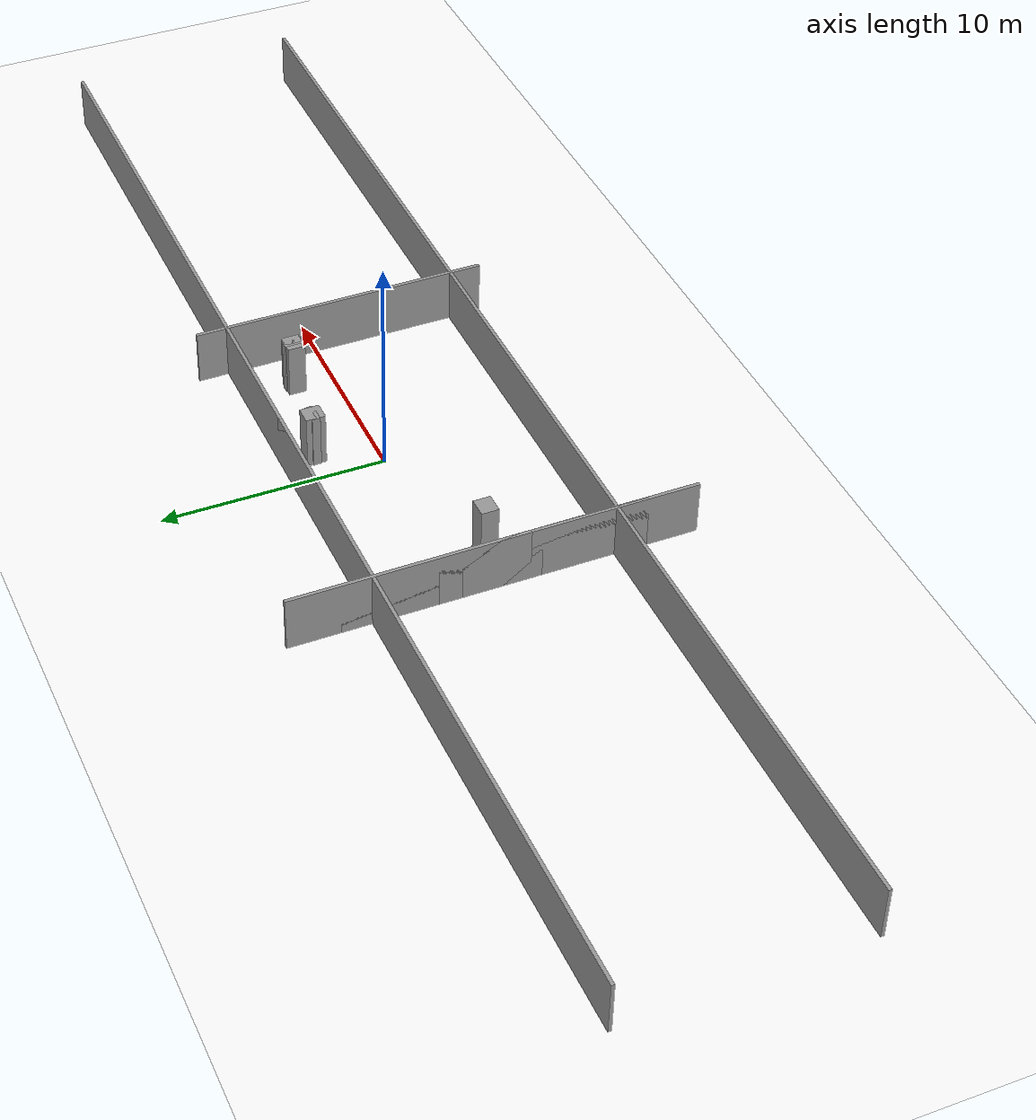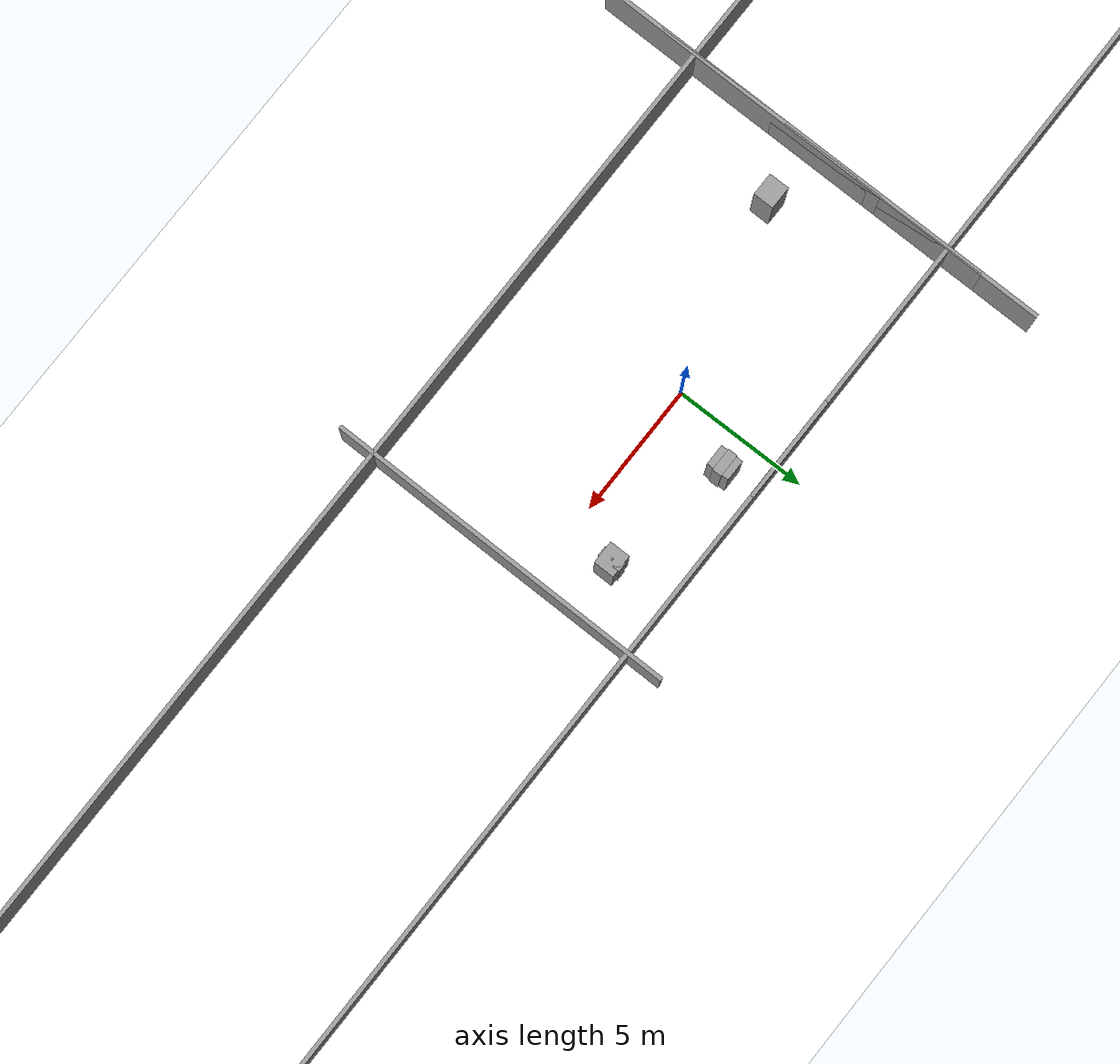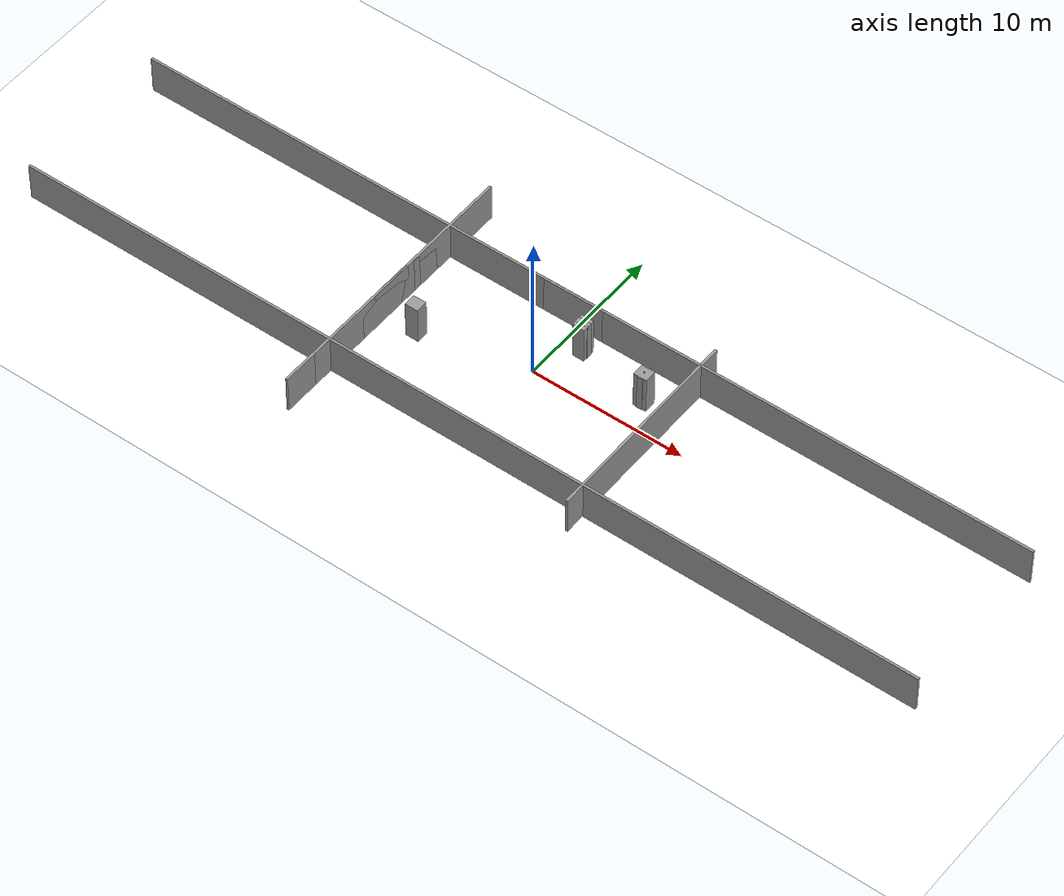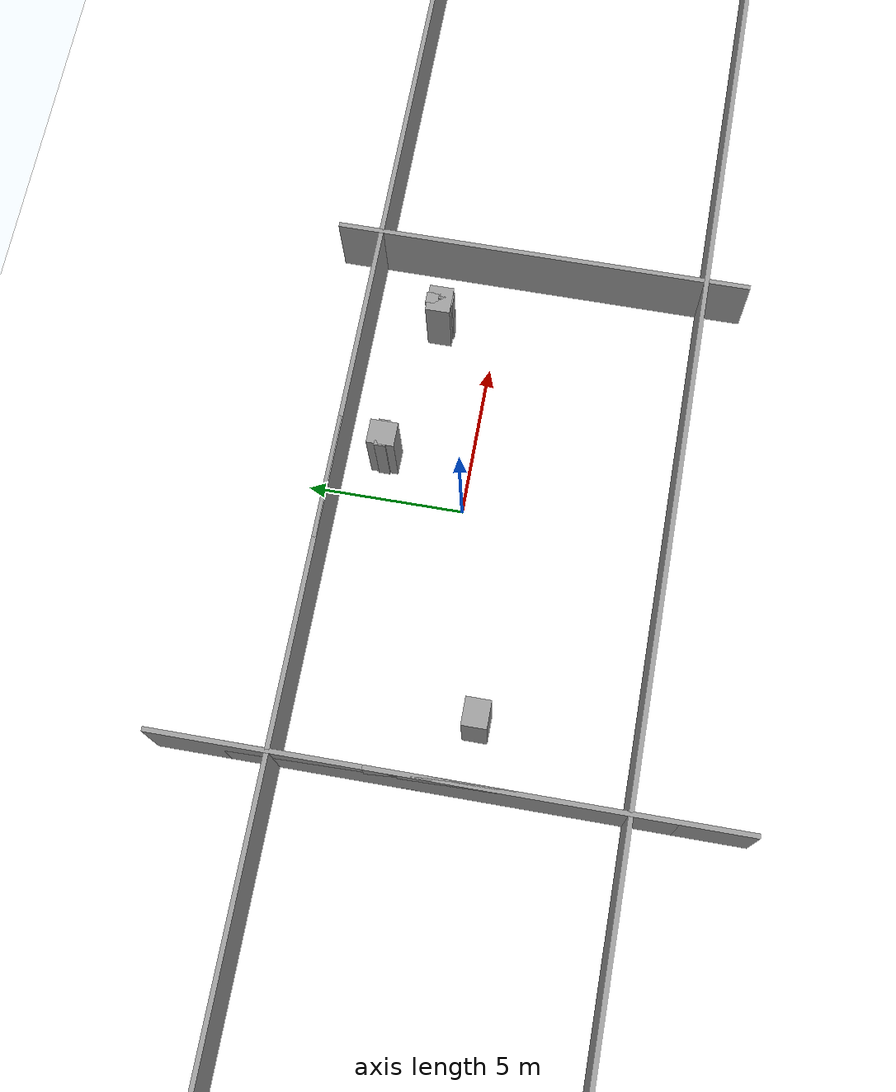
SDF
<sdf version="1.7">
 <world name="default">
  <light name="sun" type="directional">
   <cast_shadows>false</cast_shadows>
   <pose>0 0 10 0 -0 0</pose>
   <diffuse>0.8 0.8 0.8 1</diffuse>
   <specular>0.2 0.2 0.2 1</specular>
   <attenuation>
    <range>1000</range>
    <constant>0.9</constant>
    <linear>0.01</linear>
    <quadratic>0.001</quadratic>
   </attenuation>
   <direction>-0.5 0.1 -0.9</direction>
   <spot><inner_angle>0</inner_angle><outer_angle>0</outer_angle><falloff>0</falloff></spot>
  </light>
  <model name="ground_plane">
   <static>false</static>
   <link name="link">
    <collision name="collision">
     <geometry><plane><normal>0 0 1</normal><size>100 100</size></plane></geometry>
     <surface>
      <contact><collide_bitmask>65535</collide_bitmask></contact>
      <friction><ode><mu>100</mu><mu2>50</mu2></ode></friction>
     </surface>
    </collision>
    <visual name="visual">
     <cast_shadows>0</cast_shadows>
     <geometry><plane><normal>0 0 1</normal><size>100 100</size></plane></geometry>
     <material>
      <ambient>1 1 1 1</ambient>
      <diffuse>1 1 1 1</diffuse>
      <specular>0 0 0 1</specular>
      <emissive>0 0 0 1</emissive>
     </material>
    </visual>
   </link>
  </model>
  <gravity>0 0 -9.8</gravity>
  <magnetic_field>6e-06 2.3e-05 -4.2e-05</magnetic_field>
  <atmosphere type="adiabatic"/>
  <physics type="ode">
   <max_step_size>0.01</max_step_size>
   <real_time_update_rate>100</real_time_update_rate>
   <max_step_size>0.001</max_step_size>
   <real_time_factor>1</real_time_factor>
   <real_time_update_rate>1000</real_time_update_rate>
  </physics>
  <scene>
   <ambient>1 1 1 1</ambient>
   <background>1 1 1 1</background>
   <shadows>false</shadows>
   <shadows>false</shadows>
  </scene>
  <spherical_coordinates>
   <surface_model>EARTH_WGS84</surface_model>
   <latitude_deg>0</latitude_deg>
   <longitude_deg>0</longitude_deg>
   <elevation>0</elevation>
   <heading_deg>0</heading_deg>
  </spherical_coordinates>
  <model name="maze">
   <pose>-0.329869 -1.19874 0 0 -0 0</pose>
   <link name="Wall_301">
    <collision name="Wall_301_Collision">
     <geometry><box><size>4.0 0.15 2.5</size></box></geometry>
     <pose>0 0 1.25 0 -0 0</pose>
    </collision>
    <visual name="Wall_301_Visual">
     <pose>0 0 1.25 0 -0 0</pose>
     <geometry><box><size>4.0 0.15 2.5</size></box></geometry>
     <material>
      <script><uri>file://media/materials/scripts/gazebo.material</uri><name>Gazebo/Grey</name></script>
      <ambient>1 1 1 1</ambient>
     </material>
     <meta><layer>0</layer></meta>
    </visual>
    <pose>-0 5.3 0 0 -0 3.14159</pose>
   </link>
   <link name="Wall_302">
    <collision name="Wall_302_Collision">
     <geometry><box><size>4.0 0.15 2.5</size></box></geometry>
     <pose>0 0 1.25 0 -0 0</pose>
    </collision>
    <visual name="Wall_302_Visual">
     <pose>0 0 1.25 0 -0 0</pose>
     <geometry><box><size>4.0 0.15 2.5</size></box></geometry>
     <material>
      <script><uri>file://media/materials/scripts/gazebo.material</uri><name>Gazebo/Grey</name></script>
      <ambient>1 1 1 1</ambient>
     </material>
     <meta><layer>0</layer></meta>
    </visual>
    <pose>-0 5.3 0 0 -0 3.14159</pose>
   </link>
   <link name="Wall_303">
    <collision name="Wall_303_Collision">
     <geometry><box><size>4.0 0.15 2.5</size></box></geometry>
     <pose>0 0 1.25 0 -0 0</pose>
    </collision>
    <visual name="Wall_303_Visual">
     <pose>0 0 1.25 0 -0 0</pose>
     <geometry><box><size>4.0 0.15 2.5</size></box></geometry>
     <material>
      <script><uri>file://media/materials/scripts/gazebo.material</uri><name>Gazebo/Grey</name></script>
      <ambient>1 1 1 1</ambient>
     </material>
     <meta><layer>0</layer></meta>
    </visual>
    <pose>-0 5.3 0 0 -0 3.14159</pose>
   </link>
   <link name="Wall_02">
    <collision name="Wall_02_Collision">
     <geometry><box><size>18.0 0.15 2.5</size></box></geometry>
     <pose>0 0 1.25 0 -0 0</pose>
    </collision>
    <visual name="Wall_02_Visual">
     <pose>0 0 1.25 0 -0 0</pose>
     <geometry><box><size>18.0 0.15 2.5</size></box></geometry>
     <material>
      <script><uri>file://media/materials/scripts/gazebo.material</uri><name>Gazebo/Grey</name></script>
      <ambient>1 1 1 1</ambient>
     </material>
     <meta><layer>0</layer></meta>
    </visual>
    <pose>-8.55 0 0 0 -0 -1.5708</pose>
   </link>
   <link name="Wall_304">
    <collision name="Wall_304_Collision">
     <geometry><box><size>4.0 0.15 2.5</size></box></geometry>
     <pose>0 0 1.25 0 -0 0</pose>
    </collision>
    <visual name="Wall_304_Visual">
     <pose>0 0 1.25 0 -0 0</pose>
     <geometry><box><size>4.0 0.15 2.5</size></box></geometry>
     <material>
      <script><uri>file://media/materials/scripts/gazebo.material</uri><name>Gazebo/Grey</name></script>
      <ambient>1 1 1 1</ambient>
     </material>
     <meta><layer>0</layer></meta>
    </visual>
    <pose>-8.55 0 0 0 -0 -1.5708</pose>
   </link>
   <link name="Wall_305">
    <collision name="Wall_305_Collision">
     <geometry><box><size>5.0 0.15 2.5</size></box></geometry>
     <pose>0 0 1.25 0 -0 0</pose>
    </collision>
    <visual name="Wall_305_Visual">
     <pose>0 0 1.25 0 -0 0</pose>
     <geometry><box><size>5.0 0.15 2.5</size></box></geometry>
     <material>
      <script><uri>file://media/materials/scripts/gazebo.material</uri><name>Gazebo/Grey</name></script>
      <ambient>1 1 1 1</ambient>
     </material>
     <meta><layer>0</layer></meta>
    </visual>
    <pose>-8.55 0 0 0 -0 -1.5708</pose>
   </link>
   <link name="Wall_306">
    <collision name="Wall_306_Collision">
     <geometry><box><size>3.0 0.15 2.5</size></box></geometry>
     <pose>0 0 1.25 0 -0 0</pose>
    </collision>
    <visual name="Wall_306_Visual">
     <pose>0 0 1.25 0 -0 0</pose>
     <geometry><box><size>3.0 0.15 2.5</size></box></geometry>
     <material>
      <script><uri>file://media/materials/scripts/gazebo.material</uri><name>Gazebo/Grey</name></script>
      <ambient>1 1 1 1</ambient>
     </material>
     <meta><layer>0</layer></meta>
    </visual>
    <pose>-8.55 0 0 0 -0 -1.5708</pose>
   </link>
   <link name="Wall_307">
    <collision name="Wall_307_Collision">
     <geometry><box><size>3.0 0.15 2.5</size></box></geometry>
     <pose>0 0 1.25 0 -0 0</pose>
    </collision>
    <visual name="Wall_307_Visual">
     <pose>0 0 1.25 0 -0 0</pose>
     <geometry><box><size>3.0 0.15 2.5</size></box></geometry>
     <material>
      <script><uri>file://media/materials/scripts/gazebo.material</uri><name>Gazebo/Grey</name></script>
      <ambient>1 1 1 1</ambient>
     </material>
     <meta><layer>0</layer></meta>
    </visual>
    <pose>-8.55 0 0 0 -0 -1.5708</pose>
   </link>
   <link name="Wall_308">
    <collision name="Wall_308_Collision">
     <geometry><box><size>3.0 0.15 2.5</size></box></geometry>
     <pose>0 0 1.25 0 -0 0</pose>
    </collision>
    <visual name="Wall_308_Visual">
     <pose>0 0 1.25 0 -0 0</pose>
     <geometry><box><size>3.0 0.15 2.5</size></box></geometry>
     <material>
      <script><uri>file://media/materials/scripts/gazebo.material</uri><name>Gazebo/Grey</name></script>
      <ambient>1 1 1 1</ambient>
     </material>
     <meta><layer>0</layer></meta>
    </visual>
    <pose>-8.55 0 0 0 -0 -1.5708</pose>
   </link>
   <link name="Wall_309">
    <collision name="Wall_309_Collision">
     <geometry><box><size>3.0 0.15 2.5</size></box></geometry>
     <pose>0 0 1.25 0 -0 0</pose>
    </collision>
    <visual name="Wall_309_Visual">
     <pose>0 0 1.25 0 -0 0</pose>
     <geometry><box><size>3.0 0.15 2.5</size></box></geometry>
     <material>
      <script><uri>file://media/materials/scripts/gazebo.material</uri><name>Gazebo/Grey</name></script>
      <ambient>1 1 1 1</ambient>
     </material>
     <meta><layer>0</layer></meta>
    </visual>
    <pose>-8.55 0 0 0 -0 -1.5708</pose>
   </link>
   <link name="Wall_10">
    <collision name="Wall_10_Collision">
     <geometry><box><size>60.0 0.15 2.5</size></box></geometry>
     <pose>0 0 1.25 0 -0 0</pose>
    </collision>
    <visual name="Wall_10_Visual">
     <pose>0 0 1.25 0 -0 0</pose>
     <geometry><box><size>60.0 0.15 2.5</size></box></geometry>
     <material>
      <script><uri>file://media/materials/scripts/gazebo.material</uri><name>Gazebo/Grey</name></script>
      <ambient>1 1 1 1</ambient>
     </material>
     <meta><layer>0</layer></meta>
    </visual>
    <pose>-0 5.3 0 0 -0 3.14159</pose>
   </link>
   <link name="Wall_12">
    <collision name="Wall_12_Collision">
     <geometry><box><size>0.78 0.87 2.5</size></box></geometry>
     <pose>0 0 1.25 0 -0 0</pose>
    </collision>
    <visual name="Wall_12_Visual">
     <pose>0 0 1.25 0 -0 0</pose>
     <geometry><box><size>0.78 0.87 2.5</size></box></geometry>
     <material>
      <script><uri>file://media/materials/scripts/gazebo.material</uri><name>Gazebo/Grey</name></script>
      <ambient>1 1 1 1</ambient>
     </material>
     <meta><layer>0</layer></meta>
    </visual>
    <pose>-6.43927 -0.455016 0 0 -0 -1.5708</pose>
   </link>
   <link name="Wall_13">
    <collision name="Wall_13_Collision">
     <geometry><box><size>0.78 0.87 2.5</size></box></geometry>
     <pose>0 0 1.25 0 -0 0</pose>
    </collision>
    <visual name="Wall_13_Visual">
     <pose>0 0 1.25 0 -0 0</pose>
     <geometry><box><size>0.78 0.87 2.5</size></box></geometry>
     <material>
      <script><uri>file://media/materials/scripts/gazebo.material</uri><name>Gazebo/Grey</name></script>
      <ambient>1 1 1 1</ambient>
     </material>
     <meta><layer>0</layer></meta>
    </visual>
    <pose>-6.43927 -0.455016 0 0 -0 -1.5708</pose>
   </link>
   <link name="Wall_14">
    <collision name="Wall_14_Collision">
     <geometry><box><size>0.78 0.87 2.5</size></box></geometry>
     <pose>0 0 1.25 0 -0 0</pose>
    </collision>
    <visual name="Wall_14_Visual">
     <pose>0 0 1.25 0 -0 0</pose>
     <geometry><box><size>0.78 0.87 2.5</size></box></geometry>
     <material>
      <script><uri>file://media/materials/scripts/gazebo.material</uri><name>Gazebo/Grey</name></script>
      <ambient>1 1 1 1</ambient>
     </material>
     <meta><layer>0</layer></meta>
    </visual>
    <pose>1.66753 3.92803 0 0 -0 0</pose>
   </link>
   <link name="Wall_15">
    <collision name="Wall_15_Collision">
     <geometry><box><size>0.78 0.87 2.5</size></box></geometry>
     <pose>0 0 1.25 0 -0 0</pose>
    </collision>
    <visual name="Wall_15_Visual">
     <pose>0 0 1.25 0 -0 0</pose>
     <geometry><box><size>0.78 0.87 2.5</size></box></geometry>
     <material>
      <script><uri>file://media/materials/scripts/gazebo.material</uri><name>Gazebo/Grey</name></script>
      <ambient>1 1 1 1</ambient>
     </material>
     <meta><layer>0</layer></meta>
    </visual>
    <pose>6.4675 3.003028 0 0 -0 -1.5708</pose>
   </link>
   <link name="Wall_16">
    <collision name="Wall_16_Collision">
     <geometry><box><size>0.78 0.87 2.5</size></box></geometry>
     <pose>0 0 1.25 0 -0 0</pose>
    </collision>
    <visual name="Wall_16_Visual">
     <pose>0 0 1.25 0 -0 0</pose>
     <geometry><box><size>0.78 0.87 2.5</size></box></geometry>
     <material>
      <script><uri>file://media/materials/scripts/gazebo.material</uri><name>Gazebo/Grey</name></script>
      <ambient>1 1 1 1</ambient>
     </material>
     <meta><layer>0</layer></meta>
    </visual>
    <pose>6.4675 3.003028 0 0 -0 -1.5708</pose>
   </link>
   <link name="Wall_17">
    <collision name="Wall_17_Collision">
     <geometry><box><size>0.78 0.87 2.5</size></box></geometry>
     <pose>0 0 1.25 0 -0 0</pose>
    </collision>
    <visual name="Wall_17_Visual">
     <pose>0 0 1.25 0 -0 0</pose>
     <geometry><box><size>0.78 0.87 2.5</size></box></geometry>
     <material>
      <script><uri>file://media/materials/scripts/gazebo.material</uri><name>Gazebo/Grey</name></script>
      <ambient>1 1 1 1</ambient>
     </material>
     <meta><layer>0</layer></meta>
    </visual>
    <pose>6.4675 3.003028 0 0 -0 -1.5708</pose>
   </link>
   <link name="Wall_18">
    <collision name="Wall_18_Collision">
     <geometry><box><size>0.78 0.87 2.5</size></box></geometry>
     <pose>0 0 1.25 0 -0 0</pose>
    </collision>
    <visual name="Wall_18_Visual">
     <pose>0 0 1.25 0 -0 0</pose>
     <geometry><box><size>0.78 0.87 2.5</size></box></geometry>
     <material>
      <script><uri>file://media/materials/scripts/gazebo.material</uri><name>Gazebo/Grey</name></script>
      <ambient>1 1 1 1</ambient>
     </material>
     <meta><layer>0</layer></meta>
    </visual>
    <pose>6.4675 3.003028 0 0 -0 -1.5708</pose>
   </link>
   <link name="Wall_19">
    <collision name="Wall_19_Collision">
     <geometry><box><size>0.78 0.87 2.5</size></box></geometry>
     <pose>0 0 1.25 0 -0 0</pose>
    </collision>
    <visual name="Wall_19_Visual">
     <pose>0 0 1.25 0 -0 0</pose>
     <geometry><box><size>0.78 0.87 2.5</size></box></geometry>
     <material>
      <script><uri>file://media/materials/scripts/gazebo.material</uri><name>Gazebo/Grey</name></script>
      <ambient>1 1 1 1</ambient>
     </material>
     <meta><layer>0</layer></meta>
    </visual>
    <pose>6.4675 3.003028 0 0 -0 -1.5708</pose>
   </link>
   <link name="Wall_20">
    <collision name="Wall_20_Collision">
     <geometry><box><size>0.78 0.87 2.5</size></box></geometry>
     <pose>0 0 1.25 0 -0 0</pose>
    </collision>
    <visual name="Wall_20_Visual">
     <pose>0 0 1.25 0 -0 0</pose>
     <geometry><box><size>0.78 0.87 2.5</size></box></geometry>
     <material>
      <script><uri>file://media/materials/scripts/gazebo.material</uri><name>Gazebo/Grey</name></script>
      <ambient>1 1 1 1</ambient>
     </material>
     <meta><layer>0</layer></meta>
    </visual>
    <pose>6.4675 3.003028 0 0 -0 -1.5708</pose>
   </link>
   <link name="Wall_21">
    <collision name="Wall_21_Collision">
     <geometry><box><size>0.78 0.87 2.5</size></box></geometry>
     <pose>0 0 1.25 0 -0 0</pose>
    </collision>
    <visual name="Wall_21_Visual">
     <pose>0 0 1.25 0 -0 0</pose>
     <geometry><box><size>0.78 0.87 2.5</size></box></geometry>
     <material>
      <script><uri>file://media/materials/scripts/gazebo.material</uri><name>Gazebo/Grey</name></script>
      <ambient>1 1 1 1</ambient>
     </material>
     <meta><layer>0</layer></meta>
    </visual>
    <pose>6.4675 3.003028 0 0 -0 -1.5708</pose>
   </link>
   <link name="Wall_22">
    <collision name="Wall_22_Collision">
     <geometry><box><size>0.78 0.87 2.5</size></box></geometry>
     <pose>0 0 1.25 0 -0 0</pose>
    </collision>
    <visual name="Wall_22_Visual">
     <pose>0 0 1.25 0 -0 0</pose>
     <geometry><box><size>0.78 0.87 2.5</size></box></geometry>
     <material>
      <script><uri>file://media/materials/scripts/gazebo.material</uri><name>Gazebo/Grey</name></script>
      <ambient>1 1 1 1</ambient>
     </material>
     <meta><layer>0</layer></meta>
    </visual>
    <pose>6.4675 3.003028 0 0 -0 -1.5708</pose>
   </link>
   <link name="Wall_23">
    <collision name="Wall_23_Collision">
     <geometry><box><size>0.78 0.87 2.5</size></box></geometry>
     <pose>0 0 1.25 0 -0 0</pose>
    </collision>
    <visual name="Wall_23_Visual">
     <pose>0 0 1.25 0 -0 0</pose>
     <geometry><box><size>0.78 0.87 2.5</size></box></geometry>
     <material>
      <script><uri>file://media/materials/scripts/gazebo.material</uri><name>Gazebo/Grey</name></script>
      <ambient>1 1 1 1</ambient>
     </material>
     <meta><layer>0</layer></meta>
    </visual>
    <pose>6.4675 3.003028 0 0 -0 -1.5708</pose>
   </link>
   <link name="Wall_24">
    <collision name="Wall_24_Collision">
     <geometry><box><size>0.78 0.87 2.5</size></box></geometry>
     <pose>0 0 1.25 0 -0 0</pose>
    </collision>
    <visual name="Wall_24_Visual">
     <pose>0 0 1.25 0 -0 0</pose>
     <geometry><box><size>0.78 0.87 2.5</size></box></geometry>
     <material>
      <script><uri>file://media/materials/scripts/gazebo.material</uri><name>Gazebo/Grey</name></script>
      <ambient>1 1 1 1</ambient>
     </material>
     <meta><layer>0</layer></meta>
    </visual>
    <pose>6.4675 3.003028 0 0 -0 -1.5708</pose>
   </link>
   <link name="Wall_25">
    <collision name="Wall_25_Collision">
     <geometry><box><size>0.78 0.87 2.5</size></box></geometry>
     <pose>0 0 1.25 0 -0 0</pose>
    </collision>
    <visual name="Wall_25_Visual">
     <pose>0 0 1.25 0 -0 0</pose>
     <geometry><box><size>0.78 0.87 2.5</size></box></geometry>
     <material>
      <script><uri>file://media/materials/scripts/gazebo.material</uri><name>Gazebo/Grey</name></script>
      <ambient>1 1 1 1</ambient>
     </material>
     <meta><layer>0</layer></meta>
    </visual>
    <pose>6.4675 3.003028 0 0 -0 -1.5708</pose>
   </link>
   <link name="Wall_34">
    <collision name="Wall_34_Collision">
     <geometry><box><size>0.87 0.36  2.5</size></box></geometry>
     <pose>0 0 1.25 0 -0 0</pose>
    </collision>
    <visual name="Wall_34_Visual">
     <pose>0 0 1.25 0 -0 0</pose>
     <geometry><box><size>0.87 0.36  2.5</size></box></geometry>
     <material>
      <script><uri>file://media/materials/scripts/gazebo.material</uri><name>Gazebo/Grey</name></script>
      <ambient>1 1 1 1</ambient>
     </material>
     <meta><layer>0</layer></meta>
    </visual>
    <pose>1.66753 3.92803 0 0 -0 0</pose>
   </link>
   <link name="Wall_35">
    <collision name="Wall_35_Collision">
     <geometry><box><size>0.87 0.36 2.5</size></box></geometry>
     <pose>0 0 1.25 0 -0 0</pose>
    </collision>
    <visual name="Wall_35_Visual">
     <pose>0 0 1.25 0 -0 0</pose>
     <geometry><box><size>0.87 0.36 2.5</size></box></geometry>
     <material>
      <script><uri>file://media/materials/scripts/gazebo.material</uri><name>Gazebo/Grey</name></script>
      <ambient>1 1 1 1</ambient>
     </material>
     <meta><layer>0</layer></meta>
    </visual>
    <pose>6.4675 3.003028 0 0 -0 -1.5708</pose>
   </link>
   <link name="Wall_36">
    <collision name="Wall_36_Collision">
     <geometry><box><size>0.87 0.36 2.5</size></box></geometry>
     <pose>0 0 1.25 0 -0 0</pose>
    </collision>
    <visual name="Wall_36_Visual">
     <pose>0 0 1.25 0 -0 0</pose>
     <geometry><box><size>0.87 0.36 2.5</size></box></geometry>
     <material>
      <script><uri>file://media/materials/scripts/gazebo.material</uri><name>Gazebo/Grey</name></script>
      <ambient>1 1 1 1</ambient>
     </material>
     <meta><layer>0</layer></meta>
    </visual>
    <pose>6.4675 3.003028 0 0 -0 -1.5708</pose>
   </link>
   <link name="Wall_37">
    <collision name="Wall_37_Collision">
     <geometry><box><size>0.87 0.36 2.5</size></box></geometry>
     <pose>0 0 1.25 0 -0 0</pose>
    </collision>
    <visual name="Wall_37_Visual">
     <pose>0 0 1.25 0 -0 0</pose>
     <geometry><box><size>0.87 0.36 2.5</size></box></geometry>
     <material>
      <script><uri>file://media/materials/scripts/gazebo.material</uri><name>Gazebo/Grey</name></script>
      <ambient>1 1 1 1</ambient>
     </material>
     <meta><layer>0</layer></meta>
    </visual>
    <pose>6.4675 3.003028 0 0 -0 -1.5708</pose>
   </link>
   <link name="Wall_38">
    <collision name="Wall_38_Collision">
     <geometry><box><size>0.87 0.36 2.5</size></box></geometry>
     <pose>0 0 1.25 0 -0 0</pose>
    </collision>
    <visual name="Wall_38_Visual">
     <pose>0 0 1.25 0 -0 0</pose>
     <geometry><box><size>0.87 0.36 2.5</size></box></geometry>
     <material>
      <script><uri>file://media/materials/scripts/gazebo.material</uri><name>Gazebo/Grey</name></script>
      <ambient>1 1 1 1</ambient>
     </material>
     <meta><layer>0</layer></meta>
    </visual>
    <pose>6.4675 3.003028 0 0 -0 -1.5708</pose>
   </link>
   <link name="Wall_39">
    <collision name="Wall_39_Collision">
     <geometry><box><size>0.87 0.36 2.5</size></box></geometry>
     <pose>0 0 1.25 0 -0 0</pose>
    </collision>
    <visual name="Wall_39_Visual">
     <pose>0 0 1.25 0 -0 0</pose>
     <geometry><box><size>0.87 0.36 2.5</size></box></geometry>
     <material>
      <script><uri>file://media/materials/scripts/gazebo.material</uri><name>Gazebo/Grey</name></script>
      <ambient>1 1 1 1</ambient>
     </material>
     <meta><layer>0</layer></meta>
    </visual>
    <pose>6.4675 3.003028 0 0 -0 -1.5708</pose>
   </link>
   <link name="Wall_40">
    <collision name="Wall_40_Collision">
     <geometry><box><size>0.87 0.36 2.5</size></box></geometry>
     <pose>0 0 1.25 0 -0 0</pose>
    </collision>
    <visual name="Wall_40_Visual">
     <pose>0 0 1.25 0 -0 0</pose>
     <geometry><box><size>0.87 0.36 2.5</size></box></geometry>
     <material>
      <script><uri>file://media/materials/scripts/gazebo.material</uri><name>Gazebo/Grey</name></script>
      <ambient>1 1 1 1</ambient>
     </material>
     <meta><layer>0</layer></meta>
    </visual>
    <pose>6.4675 3.003028 0 0 -0 -1.5708</pose>
   </link>
   <link name="Wall_41">
    <collision name="Wall_41_Collision">
     <geometry><box><size>0.87 0.36 2.5</size></box></geometry>
     <pose>0 0 1.25 0 -0 0</pose>
    </collision>
    <visual name="Wall_41_Visual">
     <pose>0 0 1.25 0 -0 0</pose>
     <geometry><box><size>0.87 0.36 2.5</size></box></geometry>
     <material>
      <script><uri>file://media/materials/scripts/gazebo.material</uri><name>Gazebo/Grey</name></script>
      <ambient>1 1 1 1</ambient>
     </material>
     <meta><layer>0</layer></meta>
    </visual>
    <pose>6.4675 3.003028 0 0 -0 -1.5708</pose>
   </link>
   <link name="Wall_42">
    <collision name="Wall_42_Collision">
     <geometry><box><size>0.87 0.36 2.5</size></box></geometry>
     <pose>0 0 1.25 0 -0 0</pose>
    </collision>
    <visual name="Wall_42_Visual">
     <pose>0 0 1.25 0 -0 0</pose>
     <geometry><box><size>0.87 0.36 2.5</size></box></geometry>
     <material>
      <script><uri>file://media/materials/scripts/gazebo.material</uri><name>Gazebo/Grey</name></script>
      <ambient>1 1 1 1</ambient>
     </material>
     <meta><layer>0</layer></meta>
    </visual>
    <pose>6.4675 3.003028 0 0 -0 -1.5708</pose>
   </link>
   <link name="Wall_43">
    <collision name="Wall_43_Collision">
     <geometry><box><size>0.87 0.36 2.5</size></box></geometry>
     <pose>0 0 1.25 0 -0 0</pose>
    </collision>
    <visual name="Wall_43_Visual">
     <pose>0 0 1.25 0 -0 0</pose>
     <geometry><box><size>0.87 0.36 2.5</size></box></geometry>
     <material>
      <script><uri>file://media/materials/scripts/gazebo.material</uri><name>Gazebo/Grey</name></script>
      <ambient>1 1 1 1</ambient>
     </material>
     <meta><layer>0</layer></meta>
    </visual>
    <pose>6.4675 3.003028 0 0 -0 -1.5708</pose>
   </link>
   <link name="Wall_44">
    <collision name="Wall_44_Collision">
     <geometry><box><size>0.87 0.36 2.5</size></box></geometry>
     <pose>0 0 1.25 0 -0 0</pose>
    </collision>
    <visual name="Wall_44_Visual">
     <pose>0 0 1.25 0 -0 0</pose>
     <geometry><box><size>0.87 0.36 2.5</size></box></geometry>
     <material>
      <script><uri>file://media/materials/scripts/gazebo.material</uri><name>Gazebo/Grey</name></script>
      <ambient>1 1 1 1</ambient>
     </material>
     <meta><layer>0</layer></meta>
    </visual>
    <pose>6.4675 3.003028 0 0 -0 -1.5708</pose>
   </link>
   <link name="Wall_45">
    <collision name="Wall_45_Collision">
     <geometry><box><size>0.87 0.36 2.5</size></box></geometry>
     <pose>0 0 1.25 0 -0 0</pose>
    </collision>
    <visual name="Wall_45_Visual">
     <pose>0 0 1.25 0 -0 0</pose>
     <geometry><box><size>0.87 0.36 2.5</size></box></geometry>
     <material>
      <script><uri>file://media/materials/scripts/gazebo.material</uri><name>Gazebo/Grey</name></script>
      <ambient>1 1 1 1</ambient>
     </material>
     <meta><layer>0</layer></meta>
    </visual>
    <pose>6.4675 3.003028 0 0 -0 -1.5708</pose>
   </link>
   <link name="Wall_52">
    <collision name="Wall_52_Collision">
     <geometry><box><size>0.78 0.87 2.5</size></box></geometry>
     <pose>0 0 1.25 0 -0 0</pose>
    </collision>
    <visual name="Wall_52_Visual">
     <pose>0 0 1.25 0 -0 0</pose>
     <geometry><box><size>0.78 0.87 2.5</size></box></geometry>
     <material>
      <script><uri>file://media/materials/scripts/gazebo.material</uri><name>Gazebo/Grey</name></script>
      <ambient>1 1 1 1</ambient>
     </material>
     <meta><layer>0</layer></meta>
    </visual>
    <pose>-6.43927 -0.455016 0 0 -0 -1.5708</pose>
   </link>
   <link name="Wall_53">
    <collision name="Wall_53_Collision">
     <geometry><box><size>0.78 0.87 2.5</size></box></geometry>
     <pose>0 0 1.25 0 -0 0</pose>
    </collision>
    <visual name="Wall_53_Visual">
     <pose>0 0 1.25 0 -0 0</pose>
     <geometry><box><size>0.78 0.87 2.5</size></box></geometry>
     <material>
      <script><uri>file://media/materials/scripts/gazebo.material</uri><name>Gazebo/Grey</name></script>
      <ambient>1 1 1 1</ambient>
     </material>
     <meta><layer>0</layer></meta>
    </visual>
    <pose>-6.43927 -0.455016 0 0 -0 -1.5708</pose>
   </link>
   <link name="Wall_54">
    <collision name="Wall_54_Collision">
     <geometry><box><size>0.78 0.87 2.5</size></box></geometry>
     <pose>0 0 1.25 0 -0 0</pose>
    </collision>
    <visual name="Wall_54_Visual">
     <pose>0 0 1.25 0 -0 0</pose>
     <geometry><box><size>0.78 0.87 2.5</size></box></geometry>
     <material>
      <script><uri>file://media/materials/scripts/gazebo.material</uri><name>Gazebo/Grey</name></script>
      <ambient>1 1 1 1</ambient>
     </material>
     <meta><layer>0</layer></meta>
    </visual>
    <pose>1.66753 3.92803 0 0 -0 0</pose>
   </link>
   <link name="Wall_55">
    <collision name="Wall_55_Collision">
     <geometry><box><size>0.78 0.87 2.5</size></box></geometry>
     <pose>0 0 1.25 0 -0 0</pose>
    </collision>
    <visual name="Wall_55_Visual">
     <pose>0 0 1.25 0 -0 0</pose>
     <geometry><box><size>0.78 0.87 2.5</size></box></geometry>
     <material>
      <script><uri>file://media/materials/scripts/gazebo.material</uri><name>Gazebo/Grey</name></script>
      <ambient>1 1 1 1</ambient>
     </material>
     <meta><layer>0</layer></meta>
    </visual>
    <pose>6.4675 3.003028 0 0 -0 -1.5708</pose>
   </link>
   <link name="Wall_56">
    <collision name="Wall_56_Collision">
     <geometry><box><size>0.78 0.87 2.5</size></box></geometry>
     <pose>0 0 1.25 0 -0 0</pose>
    </collision>
    <visual name="Wall_56_Visual">
     <pose>0 0 1.25 0 -0 0</pose>
     <geometry><box><size>0.78 0.87 2.5</size></box></geometry>
     <material>
      <script><uri>file://media/materials/scripts/gazebo.material</uri><name>Gazebo/Grey</name></script>
      <ambient>1 1 1 1</ambient>
     </material>
     <meta><layer>0</layer></meta>
    </visual>
    <pose>6.4675 3.003028 0 0 -0 -1.5708</pose>
   </link>
   <link name="Wall_57">
    <collision name="Wall_57_Collision">
     <geometry><box><size>0.78 0.87 2.5</size></box></geometry>
     <pose>0 0 1.25 0 -0 0</pose>
    </collision>
    <visual name="Wall_57_Visual">
     <pose>0 0 1.25 0 -0 0</pose>
     <geometry><box><size>0.78 0.87 2.5</size></box></geometry>
     <material>
      <script><uri>file://media/materials/scripts/gazebo.material</uri><name>Gazebo/Grey</name></script>
      <ambient>1 1 1 1</ambient>
     </material>
     <meta><layer>0</layer></meta>
    </visual>
    <pose>6.4675 3.003028 0 0 -0 -1.5708</pose>
   </link>
   <link name="Wall_58">
    <collision name="Wall_58_Collision">
     <geometry><box><size>0.78 0.87 2.5</size></box></geometry>
     <pose>0 0 1.25 0 -0 0</pose>
    </collision>
    <visual name="Wall_58_Visual">
     <pose>0 0 1.25 0 -0 0</pose>
     <geometry><box><size>0.78 0.87 2.5</size></box></geometry>
     <material>
      <script><uri>file://media/materials/scripts/gazebo.material</uri><name>Gazebo/Grey</name></script>
      <ambient>1 1 1 1</ambient>
     </material>
     <meta><layer>0</layer></meta>
    </visual>
    <pose>6.4675 3.003028 0 0 -0 -1.5708</pose>
   </link>
   <link name="Wall_59">
    <collision name="Wall_59_Collision">
     <geometry><box><size>0.78 0.87 2.5</size></box></geometry>
     <pose>0 0 1.25 0 -0 0</pose>
    </collision>
    <visual name="Wall_59_Visual">
     <pose>0 0 1.25 0 -0 0</pose>
     <geometry><box><size>0.78 0.87 2.5</size></box></geometry>
     <material>
      <script><uri>file://media/materials/scripts/gazebo.material</uri><name>Gazebo/Grey</name></script>
      <ambient>1 1 1 1</ambient>
     </material>
     <meta><layer>0</layer></meta>
    </visual>
    <pose>6.4675 3.003028 0 0 -0 -1.5708</pose>
   </link>
   <link name="Wall_60">
    <collision name="Wall_60_Collision">
     <geometry><box><size>0.78 0.87 2.5</size></box></geometry>
     <pose>0 0 1.25 0 -0 0</pose>
    </collision>
    <visual name="Wall_60_Visual">
     <pose>0 0 1.25 0 -0 0</pose>
     <geometry><box><size>0.78 0.87 2.5</size></box></geometry>
     <material>
      <script><uri>file://media/materials/scripts/gazebo.material</uri><name>Gazebo/Grey</name></script>
      <ambient>1 1 1 1</ambient>
     </material>
     <meta><layer>0</layer></meta>
    </visual>
    <pose>6.4675 3.003028 0 0 -0 -1.5708</pose>
   </link>
   <link name="Wall_61">
    <collision name="Wall_61_Collision">
     <geometry><box><size>0.78 0.87 2.5</size></box></geometry>
     <pose>0 0 1.25 0 -0 0</pose>
    </collision>
    <visual name="Wall_61_Visual">
     <pose>0 0 1.25 0 -0 0</pose>
     <geometry><box><size>0.78 0.87 2.5</size></box></geometry>
     <material>
      <script><uri>file://media/materials/scripts/gazebo.material</uri><name>Gazebo/Grey</name></script>
      <ambient>1 1 1 1</ambient>
     </material>
     <meta><layer>0</layer></meta>
    </visual>
    <pose>6.4675 3.003028 0 0 -0 -1.5708</pose>
   </link>
   <link name="Wall_62">
    <collision name="Wall_62_Collision">
     <geometry><box><size>0.78 0.87 2.5</size></box></geometry>
     <pose>0 0 1.25 0 -0 0</pose>
    </collision>
    <visual name="Wall_62_Visual">
     <pose>0 0 1.25 0 -0 0</pose>
     <geometry><box><size>0.78 0.87 2.5</size></box></geometry>
     <material>
      <script><uri>file://media/materials/scripts/gazebo.material</uri><name>Gazebo/Grey</name></script>
      <ambient>1 1 1 1</ambient>
     </material>
     <meta><layer>0</layer></meta>
    </visual>
    <pose>6.4675 3.003028 0 0 -0 -1.5708</pose>
   </link>
   <link name="Wall_63">
    <collision name="Wall_63_Collision">
     <geometry><box><size>0.78 0.87 2.5</size></box></geometry>
     <pose>0 0 1.25 0 -0 0</pose>
    </collision>
    <visual name="Wall_63_Visual">
     <pose>0 0 1.25 0 -0 0</pose>
     <geometry><box><size>0.78 0.87 2.5</size></box></geometry>
     <material>
      <script><uri>file://media/materials/scripts/gazebo.material</uri><name>Gazebo/Grey</name></script>
      <ambient>1 1 1 1</ambient>
     </material>
     <meta><layer>0</layer></meta>
    </visual>
    <pose>6.4675 3.003028 0 0 -0 -1.5708</pose>
   </link>
   <link name="Wall_64">
    <collision name="Wall_64_Collision">
     <geometry><box><size>0.78 0.87 2.5</size></box></geometry>
     <pose>0 0 1.25 0 -0 0</pose>
    </collision>
    <visual name="Wall_64_Visual">
     <pose>0 0 1.25 0 -0 0</pose>
     <geometry><box><size>0.78 0.87 2.5</size></box></geometry>
     <material>
      <script><uri>file://media/materials/scripts/gazebo.material</uri><name>Gazebo/Grey</name></script>
      <ambient>1 1 1 1</ambient>
     </material>
     <meta><layer>0</layer></meta>
    </visual>
    <pose>6.4675 3.003028 0 0 -0 -1.5708</pose>
   </link>
   <link name="Wall_65">
    <collision name="Wall_65_Collision">
     <geometry><box><size>0.78 0.87 2.5</size></box></geometry>
     <pose>0 0 1.25 0 -0 0</pose>
    </collision>
    <visual name="Wall_65_Visual">
     <pose>0 0 1.25 0 -0 0</pose>
     <geometry><box><size>0.78 0.87 2.5</size></box></geometry>
     <material>
      <script><uri>file://media/materials/scripts/gazebo.material</uri><name>Gazebo/Grey</name></script>
      <ambient>1 1 1 1</ambient>
     </material>
     <meta><layer>0</layer></meta>
    </visual>
    <pose>6.4675 3.003028 0 0 -0 -1.5708</pose>
   </link>
   <link name="Wall_74">
    <collision name="Wall_74_Collision">
     <geometry><box><size>0.87 0.36  2.5</size></box></geometry>
     <pose>0 0 1.25 0 -0 0</pose>
    </collision>
    <visual name="Wall_74_Visual">
     <pose>0 0 1.25 0 -0 0</pose>
     <geometry><box><size>0.87 0.36  2.5</size></box></geometry>
     <material>
      <script><uri>file://media/materials/scripts/gazebo.material</uri><name>Gazebo/Grey</name></script>
      <ambient>1 1 1 1</ambient>
     </material>
     <meta><layer>0</layer></meta>
    </visual>
    <pose>1.66753 3.92803 0 0 -0 0</pose>
   </link>
   <link name="Wall_75">
    <collision name="Wall_75_Collision">
     <geometry><box><size>0.87 0.36 2.5</size></box></geometry>
     <pose>0 0 1.25 0 -0 0</pose>
    </collision>
    <visual name="Wall_75_Visual">
     <pose>0 0 1.25 0 -0 0</pose>
     <geometry><box><size>0.87 0.36 2.5</size></box></geometry>
     <material>
      <script><uri>file://media/materials/scripts/gazebo.material</uri><name>Gazebo/Grey</name></script>
      <ambient>1 1 1 1</ambient>
     </material>
     <meta><layer>0</layer></meta>
    </visual>
    <pose>6.4675 3.003028 0 0 -0 -1.5708</pose>
   </link>
   <link name="Wall_76">
    <collision name="Wall_76_Collision">
     <geometry><box><size>0.87 0.36 2.5</size></box></geometry>
     <pose>0 0 1.25 0 -0 0</pose>
    </collision>
    <visual name="Wall_76_Visual">
     <pose>0 0 1.25 0 -0 0</pose>
     <geometry><box><size>0.87 0.36 2.5</size></box></geometry>
     <material>
      <script><uri>file://media/materials/scripts/gazebo.material</uri><name>Gazebo/Grey</name></script>
      <ambient>1 1 1 1</ambient>
     </material>
     <meta><layer>0</layer></meta>
    </visual>
    <pose>6.4675 3.003028 0 0 -0 -1.5708</pose>
   </link>
   <link name="Wall_77">
    <collision name="Wall_77_Collision">
     <geometry><box><size>0.87 0.36 2.5</size></box></geometry>
     <pose>0 0 1.25 0 -0 0</pose>
    </collision>
    <visual name="Wall_77_Visual">
     <pose>0 0 1.25 0 -0 0</pose>
     <geometry><box><size>0.87 0.36 2.5</size></box></geometry>
     <material>
      <script><uri>file://media/materials/scripts/gazebo.material</uri><name>Gazebo/Grey</name></script>
      <ambient>1 1 1 1</ambient>
     </material>
     <meta><layer>0</layer></meta>
    </visual>
    <pose>6.4675 3.003028 0 0 -0 -1.5708</pose>
   </link>
   <link name="Wall_78">
    <collision name="Wall_78_Collision">
     <geometry><box><size>0.87 0.36 2.5</size></box></geometry>
     <pose>0 0 1.25 0 -0 0</pose>
    </collision>
    <visual name="Wall_78_Visual">
     <pose>0 0 1.25 0 -0 0</pose>
     <geometry><box><size>0.87 0.36 2.5</size></box></geometry>
     <material>
      <script><uri>file://media/materials/scripts/gazebo.material</uri><name>Gazebo/Grey</name></script>
      <ambient>1 1 1 1</ambient>
     </material>
     <meta><layer>0</layer></meta>
    </visual>
    <pose>6.4675 3.003028 0 0 -0 -1.5708</pose>
   </link>
   <link name="Wall_79">
    <collision name="Wall_79_Collision">
     <geometry><box><size>0.87 0.36 2.5</size></box></geometry>
     <pose>0 0 1.25 0 -0 0</pose>
    </collision>
    <visual name="Wall_79_Visual">
     <pose>0 0 1.25 0 -0 0</pose>
     <geometry><box><size>0.87 0.36 2.5</size></box></geometry>
     <material>
      <script><uri>file://media/materials/scripts/gazebo.material</uri><name>Gazebo/Grey</name></script>
      <ambient>1 1 1 1</ambient>
     </material>
     <meta><layer>0</layer></meta>
    </visual>
    <pose>6.4675 3.003028 0 0 -0 -1.5708</pose>
   </link>
   <link name="Wall_80">
    <collision name="Wall_80_Collision">
     <geometry><box><size>0.87 0.36 2.5</size></box></geometry>
     <pose>0 0 1.25 0 -0 0</pose>
    </collision>
    <visual name="Wall_80_Visual">
     <pose>0 0 1.25 0 -0 0</pose>
     <geometry><box><size>0.87 0.36 2.5</size></box></geometry>
     <material>
      <script><uri>file://media/materials/scripts/gazebo.material</uri><name>Gazebo/Grey</name></script>
      <ambient>1 1 1 1</ambient>
     </material>
     <meta><layer>0</layer></meta>
    </visual>
    <pose>6.4675 3.003028 0 0 -0 -1.5708</pose>
   </link>
   <link name="Wall_81">
    <collision name="Wall_81_Collision">
     <geometry><box><size>0.87 0.36 2.5</size></box></geometry>
     <pose>0 0 1.25 0 -0 0</pose>
    </collision>
    <visual name="Wall_81_Visual">
     <pose>0 0 1.25 0 -0 0</pose>
     <geometry><box><size>0.87 0.36 2.5</size></box></geometry>
     <material>
      <script><uri>file://media/materials/scripts/gazebo.material</uri><name>Gazebo/Grey</name></script>
      <ambient>1 1 1 1</ambient>
     </material>
     <meta><layer>0</layer></meta>
    </visual>
    <pose>6.4675 3.003028 0 0 -0 -1.5708</pose>
   </link>
   <link name="Wall_82">
    <collision name="Wall_82_Collision">
     <geometry><box><size>0.87 0.36 2.5</size></box></geometry>
     <pose>0 0 1.25 0 -0 0</pose>
    </collision>
    <visual name="Wall_82_Visual">
     <pose>0 0 1.25 0 -0 0</pose>
     <geometry><box><size>0.87 0.36 2.5</size></box></geometry>
     <material>
      <script><uri>file://media/materials/scripts/gazebo.material</uri><name>Gazebo/Grey</name></script>
      <ambient>1 1 1 1</ambient>
     </material>
     <meta><layer>0</layer></meta>
    </visual>
    <pose>6.4675 3.003028 0 0 -0 -1.5708</pose>
   </link>
   <link name="Wall_83">
    <collision name="Wall_83_Collision">
     <geometry><box><size>0.87 0.36 2.5</size></box></geometry>
     <pose>0 0 1.25 0 -0 0</pose>
    </collision>
    <visual name="Wall_83_Visual">
     <pose>0 0 1.25 0 -0 0</pose>
     <geometry><box><size>0.87 0.36 2.5</size></box></geometry>
     <material>
      <script><uri>file://media/materials/scripts/gazebo.material</uri><name>Gazebo/Grey</name></script>
      <ambient>1 1 1 1</ambient>
     </material>
     <meta><layer>0</layer></meta>
    </visual>
    <pose>6.4675 3.003028 0 0 -0 -1.5708</pose>
   </link>
   <link name="Wall_84">
    <collision name="Wall_84_Collision">
     <geometry><box><size>0.87 0.36 2.5</size></box></geometry>
     <pose>0 0 1.25 0 -0 0</pose>
    </collision>
    <visual name="Wall_84_Visual">
     <pose>0 0 1.25 0 -0 0</pose>
     <geometry><box><size>0.87 0.36 2.5</size></box></geometry>
     <material>
      <script><uri>file://media/materials/scripts/gazebo.material</uri><name>Gazebo/Grey</name></script>
      <ambient>1 1 1 1</ambient>
     </material>
     <meta><layer>0</layer></meta>
    </visual>
    <pose>6.4675 3.003028 0 0 -0 -1.5708</pose>
   </link>
   <link name="Wall_85">
    <collision name="Wall_85_Collision">
     <geometry><box><size>0.87 0.36 2.5</size></box></geometry>
     <pose>0 0 1.25 0 -0 0</pose>
    </collision>
    <visual name="Wall_85_Visual">
     <pose>0 0 1.25 0 -0 0</pose>
     <geometry><box><size>0.87 0.36 2.5</size></box></geometry>
     <material>
      <script><uri>file://media/materials/scripts/gazebo.material</uri><name>Gazebo/Grey</name></script>
      <ambient>1 1 1 1</ambient>
     </material>
     <meta><layer>0</layer></meta>
    </visual>
    <pose>6.4675 3.003028 0 0 -0 -1.5708</pose>
   </link>
   <link name="Wall_86">
    <collision name="Wall_86_Collision">
     <geometry><box><size>0.87 0.36 2.5</size></box></geometry>
     <pose>0 0 1.25 0 -0 0</pose>
    </collision>
    <visual name="Wall_86_Visual">
     <pose>0 0 1.25 0 -0 0</pose>
     <geometry><box><size>0.87 0.36 2.5</size></box></geometry>
     <material>
      <script><uri>file://media/materials/scripts/gazebo.material</uri><name>Gazebo/Grey</name></script>
      <ambient>1 1 1 1</ambient>
     </material>
     <meta><layer>0</layer></meta>
    </visual>
    <pose>6.4675 3.003028 0 0 -0 -1.5708</pose>
   </link>
   <link name="Wall_100">
    <collision name="Wall_100_Collision">
     <geometry><box><size>0.072 0.072 2.7</size></box></geometry>
     <pose>0 0 1.25 0 -0 0</pose>
    </collision>
    <visual name="Wall_100_Visual">
     <pose>0 0 1.25 0 -0 0</pose>
     <geometry><box><size>0.072 0.072 2.7</size></box></geometry>
     <material>
      <script><uri>file://media/materials/scripts/gazebo.material</uri><name>Gazebo/Grey</name></script>
      <ambient>1 1 1 1</ambient>
     </material>
     <meta><layer>0</layer></meta>
    </visual>
    <pose>6.4675 3.003028 0 0 -0 -1.5708</pose>
   </link>
   <link name="Wall_101">
    <collision name="Wall_101_Collision">
     <geometry><box><size>0.072 0.072 2.7</size></box></geometry>
     <pose>0 0 1.25 0 -0 0</pose>
    </collision>
    <visual name="Wall_101_Visual">
     <pose>0 0 1.25 0 -0 0</pose>
     <geometry><box><size>0.072 0.072 2.7</size></box></geometry>
     <material>
      <script><uri>file://media/materials/scripts/gazebo.material</uri><name>Gazebo/Grey</name></script>
      <ambient>1 1 1 1</ambient>
     </material>
     <meta><layer>0</layer></meta>
    </visual>
    <pose>6.4675 3.003028 0 0 -0 -1.5708</pose>
   </link>
   <link name="Wall_102">
    <collision name="Wall_102_Collision">
     <geometry><box><size>0.072 0.072 2.7</size></box></geometry>
     <pose>0 0 1.25 0 -0 0</pose>
    </collision>
    <visual name="Wall_102_Visual">
     <pose>0 0 1.25 0 -0 0</pose>
     <geometry><box><size>0.072 0.072 2.7</size></box></geometry>
     <material>
      <script><uri>file://media/materials/scripts/gazebo.material</uri><name>Gazebo/Grey</name></script>
      <ambient>1 1 1 1</ambient>
     </material>
     <meta><layer>0</layer></meta>
    </visual>
    <pose>6.4675 3.003028 0 0 -0 -1.5708</pose>
   </link>
   <link name="Wall_103">
    <collision name="Wall_103_Collision">
     <geometry><box><size>0.072 0.072 2.7</size></box></geometry>
     <pose>0 0 1.25 0 -0 0</pose>
    </collision>
    <visual name="Wall_103_Visual">
     <pose>0 0 1.25 0 -0 0</pose>
     <geometry><box><size>0.072 0.072 2.7</size></box></geometry>
     <material>
      <script><uri>file://media/materials/scripts/gazebo.material</uri><name>Gazebo/Grey</name></script>
      <ambient>1 1 1 1</ambient>
     </material>
     <meta><layer>0</layer></meta>
    </visual>
    <pose>6.4675 3.003028 0 0 -0 -1.5708</pose>
   </link>
   <link name="Wall_104">
    <collision name="Wall_104_Collision">
     <geometry><box><size>0.072 0.072 2.7</size></box></geometry>
     <pose>0 0 1.25 0 -0 0</pose>
    </collision>
    <visual name="Wall_104_Visual">
     <pose>0 0 1.25 0 -0 0</pose>
     <geometry><box><size>0.072 0.072 2.7</size></box></geometry>
     <material>
      <script><uri>file://media/materials/scripts/gazebo.material</uri><name>Gazebo/Grey</name></script>
      <ambient>1 1 1 1</ambient>
     </material>
     <meta><layer>0</layer></meta>
    </visual>
    <pose>6.4675 3.003028 0 0 -0 -1.5708</pose>
   </link>
   <link name="Wall_105">
    <collision name="Wall_105_Collision">
     <geometry><box><size>0.072 0.072 2.7</size></box></geometry>
     <pose>0 0 1.25 0 -0 0</pose>
    </collision>
    <visual name="Wall_105_Visual">
     <pose>0 0 1.25 0 -0 0</pose>
     <geometry><box><size>0.072 0.072 2.7</size></box></geometry>
     <material>
      <script><uri>file://media/materials/scripts/gazebo.material</uri><name>Gazebo/Grey</name></script>
      <ambient>1 1 1 1</ambient>
     </material>
     <meta><layer>0</layer></meta>
    </visual>
    <pose>6.4675 3.003028 0 0 -0 -1.5708</pose>
   </link>
   <link name="Wall_106">
    <collision name="Wall_106_Collision">
     <geometry><box><size>0.072 0.072 2.7</size></box></geometry>
     <pose>0 0 1.25 0 -0 0</pose>
    </collision>
    <visual name="Wall_106_Visual">
     <pose>0 0 1.25 0 -0 0</pose>
     <geometry><box><size>0.072 0.072 2.7</size></box></geometry>
     <material>
      <script><uri>file://media/materials/scripts/gazebo.material</uri><name>Gazebo/Grey</name></script>
      <ambient>1 1 1 1</ambient>
     </material>
     <meta><layer>0</layer></meta>
    </visual>
    <pose>6.4675 3.003028 0 0 -0 -1.5708</pose>
   </link>
   <link name="Wall_107">
    <collision name="Wall_107_Collision">
     <geometry><box><size>0.072 0.072 2.7</size></box></geometry>
     <pose>0 0 1.25 0 -0 0</pose>
    </collision>
    <visual name="Wall_107_Visual">
     <pose>0 0 1.25 0 -0 0</pose>
     <geometry><box><size>0.072 0.072 2.7</size></box></geometry>
     <material>
      <script><uri>file://media/materials/scripts/gazebo.material</uri><name>Gazebo/Grey</name></script>
      <ambient>1 1 1 1</ambient>
     </material>
     <meta><layer>0</layer></meta>
    </visual>
    <pose>6.4675 3.003028 0 0 -0 -1.5708</pose>
   </link>
   <link name="Wall_108">
    <collision name="Wall_108_Collision">
     <geometry><box><size>0.072 0.072 2.7</size></box></geometry>
     <pose>0 0 1.25 0 -0 0</pose>
    </collision>
    <visual name="Wall_108_Visual">
     <pose>0 0 1.25 0 -0 0</pose>
     <geometry><box><size>0.072 0.072 2.7</size></box></geometry>
     <material>
      <script><uri>file://media/materials/scripts/gazebo.material</uri><name>Gazebo/Grey</name></script>
      <ambient>1 1 1 1</ambient>
     </material>
     <meta><layer>0</layer></meta>
    </visual>
    <pose>6.4675 3.003028 0 0 -0 -1.5708</pose>
   </link>
   <link name="Wall_109">
    <collision name="Wall_109_Collision">
     <geometry><box><size>0.072 0.072 2.7</size></box></geometry>
     <pose>0 0 1.25 0 -0 0</pose>
    </collision>
    <visual name="Wall_109_Visual">
     <pose>0 0 1.25 0 -0 0</pose>
     <geometry><box><size>0.072 0.072 2.7</size></box></geometry>
     <material>
      <script><uri>file://media/materials/scripts/gazebo.material</uri><name>Gazebo/Grey</name></script>
      <ambient>1 1 1 1</ambient>
     </material>
     <meta><layer>0</layer></meta>
    </visual>
    <pose>6.4675 3.003028 0 0 -0 -1.5708</pose>
   </link>
   <link name="Wall_110">
    <collision name="Wall_110_Collision">
     <geometry><box><size>0.072 0.072 2.7</size></box></geometry>
     <pose>0 0 1.25 0 -0 0</pose>
    </collision>
    <visual name="Wall_110_Visual">
     <pose>0 0 1.25 0 -0 0</pose>
     <geometry><box><size>0.072 0.072 2.7</size></box></geometry>
     <material>
      <script><uri>file://media/materials/scripts/gazebo.material</uri><name>Gazebo/Grey</name></script>
      <ambient>1 1 1 1</ambient>
     </material>
     <meta><layer>0</layer></meta>
    </visual>
    <pose>6.4675 3.003028 0 0 -0 -1.5708</pose>
   </link>
   <link name="Wall_111">
    <collision name="Wall_111_Collision">
     <geometry><box><size>0.072 0.072 2.7</size></box></geometry>
     <pose>0 0 1.25 0 -0 0</pose>
    </collision>
    <visual name="Wall_111_Visual">
     <pose>0 0 1.25 0 -0 0</pose>
     <geometry><box><size>0.072 0.072 2.7</size></box></geometry>
     <material>
      <script><uri>file://media/materials/scripts/gazebo.material</uri><name>Gazebo/Grey</name></script>
      <ambient>1 1 1 1</ambient>
     </material>
     <meta><layer>0</layer></meta>
    </visual>
    <pose>6.4675 3.003028 0 0 -0 -1.5708</pose>
   </link>
   <link name="Wall_112">
    <collision name="Wall_112_Collision">
     <geometry><box><size>0.072 0.072 2.7</size></box></geometry>
     <pose>0 0 1.25 0 -0 0</pose>
    </collision>
    <visual name="Wall_112_Visual">
     <pose>0 0 1.25 0 -0 0</pose>
     <geometry><box><size>0.072 0.072 2.7</size></box></geometry>
     <material>
      <script><uri>file://media/materials/scripts/gazebo.material</uri><name>Gazebo/Grey</name></script>
      <ambient>1 1 1 1</ambient>
     </material>
     <meta><layer>0</layer></meta>
    </visual>
    <pose>6.4675 3.003028 0 0 -0 -1.5708</pose>
   </link>
   <link name="Wall_113">
    <collision name="Wall_113_Collision">
     <geometry><box><size>0.072 0.072 2.7</size></box></geometry>
     <pose>0 0 1.25 0 -0 0</pose>
    </collision>
    <visual name="Wall_113_Visual">
     <pose>0 0 1.25 0 -0 0</pose>
     <geometry><box><size>0.072 0.072 2.7</size></box></geometry>
     <material>
      <script><uri>file://media/materials/scripts/gazebo.material</uri><name>Gazebo/Grey</name></script>
      <ambient>1 1 1 1</ambient>
     </material>
     <meta><layer>0</layer></meta>
    </visual>
    <pose>6.4675 3.003028 0 0 -0 -1.5708</pose>
   </link>
   <link name="Wall_114">
    <collision name="Wall_114_Collision">
     <geometry><box><size>0.072 0.072 2.7</size></box></geometry>
     <pose>0 0 1.25 0 -0 0</pose>
    </collision>
    <visual name="Wall_114_Visual">
     <pose>0 0 1.25 0 -0 0</pose>
     <geometry><box><size>0.072 0.072 2.7</size></box></geometry>
     <material>
      <script><uri>file://media/materials/scripts/gazebo.material</uri><name>Gazebo/Grey</name></script>
      <ambient>1 1 1 1</ambient>
     </material>
     <meta><layer>0</layer></meta>
    </visual>
    <pose>6.4675 3.003028 0 0 -0 -1.5708</pose>
   </link>
   <link name="Wall_115">
    <collision name="Wall_115_Collision">
     <geometry><box><size>0.072 0.072 2.7</size></box></geometry>
     <pose>0 0 1.25 0 -0 0</pose>
    </collision>
    <visual name="Wall_115_Visual">
     <pose>0 0 1.25 0 -0 0</pose>
     <geometry><box><size>0.072 0.072 2.7</size></box></geometry>
     <material>
      <script><uri>file://media/materials/scripts/gazebo.material</uri><name>Gazebo/Grey</name></script>
      <ambient>1 1 1 1</ambient>
     </material>
     <meta><layer>0</layer></meta>
    </visual>
    <pose>6.4675 3.003028 0 0 -0 -1.5708</pose>
   </link>
   <link name="Wall_116">
    <collision name="Wall_116_Collision">
     <geometry><box><size>0.072 0.072 2.7</size></box></geometry>
     <pose>0 0 1.25 0 -0 0</pose>
    </collision>
    <visual name="Wall_116_Visual">
     <pose>0 0 1.25 0 -0 0</pose>
     <geometry><box><size>0.072 0.072 2.7</size></box></geometry>
     <material>
      <script><uri>file://media/materials/scripts/gazebo.material</uri><name>Gazebo/Grey</name></script>
      <ambient>1 1 1 1</ambient>
     </material>
     <meta><layer>0</layer></meta>
    </visual>
    <pose>6.4675 3.003028 0 0 -0 -1.5708</pose>
   </link>
   <link name="Wall_117">
    <collision name="Wall_117_Collision">
     <geometry><box><size>0.072 0.072 2.7</size></box></geometry>
     <pose>0 0 1.25 0 -0 0</pose>
    </collision>
    <visual name="Wall_117_Visual">
     <pose>0 0 1.25 0 -0 0</pose>
     <geometry><box><size>0.072 0.072 2.7</size></box></geometry>
     <material>
      <script><uri>file://media/materials/scripts/gazebo.material</uri><name>Gazebo/Grey</name></script>
      <ambient>1 1 1 1</ambient>
     </material>
     <meta><layer>0</layer></meta>
    </visual>
    <pose>6.4675 3.003028 0 0 -0 -1.5708</pose>
   </link>
   <link name="Wall_118">
    <collision name="Wall_118_Collision">
     <geometry><box><size>0.072 0.072 2.7</size></box></geometry>
     <pose>0 0 1.25 0 -0 0</pose>
    </collision>
    <visual name="Wall_118_Visual">
     <pose>0 0 1.25 0 -0 0</pose>
     <geometry><box><size>0.072 0.072 2.7</size></box></geometry>
     <material>
      <script><uri>file://media/materials/scripts/gazebo.material</uri><name>Gazebo/Grey</name></script>
      <ambient>1 1 1 1</ambient>
     </material>
     <meta><layer>0</layer></meta>
    </visual>
    <pose>6.4675 3.003028 0 0 -0 -1.5708</pose>
   </link>
   <link name="Wall_119">
    <collision name="Wall_119_Collision">
     <geometry><box><size>0.072 0.072 2.7</size></box></geometry>
     <pose>0 0 1.25 0 -0 0</pose>
    </collision>
    <visual name="Wall_119_Visual">
     <pose>0 0 1.25 0 -0 0</pose>
     <geometry><box><size>0.072 0.072 2.7</size></box></geometry>
     <material>
      <script><uri>file://media/materials/scripts/gazebo.material</uri><name>Gazebo/Grey</name></script>
      <ambient>1 1 1 1</ambient>
     </material>
     <meta><layer>0</layer></meta>
    </visual>
    <pose>6.4675 3.003028 0 0 -0 -1.5708</pose>
   </link>
   <link name="Wall_120">
    <collision name="Wall_120_Collision">
     <geometry><box><size>0.072 0.072 2.7</size></box></geometry>
     <pose>0 0 1.25 0 -0 0</pose>
    </collision>
    <visual name="Wall_120_Visual">
     <pose>0 0 1.25 0 -0 0</pose>
     <geometry><box><size>0.072 0.072 2.7</size></box></geometry>
     <material>
      <script><uri>file://media/materials/scripts/gazebo.material</uri><name>Gazebo/Grey</name></script>
      <ambient>1 1 1 1</ambient>
     </material>
     <meta><layer>0</layer></meta>
    </visual>
    <pose>6.4675 3.003028 0 0 -0 -1.5708</pose>
   </link>
   <link name="Wall_121">
    <collision name="Wall_121_Collision">
     <geometry><box><size>0.072 0.072 2.7</size></box></geometry>
     <pose>0 0 1.25 0 -0 0</pose>
    </collision>
    <visual name="Wall_121_Visual">
     <pose>0 0 1.25 0 -0 0</pose>
     <geometry><box><size>0.072 0.072 2.7</size></box></geometry>
     <material>
      <script><uri>file://media/materials/scripts/gazebo.material</uri><name>Gazebo/Grey</name></script>
      <ambient>1 1 1 1</ambient>
     </material>
     <meta><layer>0</layer></meta>
    </visual>
    <pose>6.4675 3.003028 0 0 -0 -1.5708</pose>
   </link>
   <link name="Wall_122">
    <collision name="Wall_122_Collision">
     <geometry><box><size>0.072 0.072 2.7</size></box></geometry>
     <pose>0 0 1.25 0 -0 0</pose>
    </collision>
    <visual name="Wall_122_Visual">
     <pose>0 0 1.25 0 -0 0</pose>
     <geometry><box><size>0.072 0.072 2.7</size></box></geometry>
     <material>
      <script><uri>file://media/materials/scripts/gazebo.material</uri><name>Gazebo/Grey</name></script>
      <ambient>1 1 1 1</ambient>
     </material>
     <meta><layer>0</layer></meta>
    </visual>
    <pose>6.4675 3.003028 0 0 -0 -1.5708</pose>
   </link>
   <link name="Wall_123">
    <collision name="Wall_123_Collision">
     <geometry><box><size>0.072 0.072 2.7</size></box></geometry>
     <pose>0 0 1.25 0 -0 0</pose>
    </collision>
    <visual name="Wall_123_Visual">
     <pose>0 0 1.25 0 -0 0</pose>
     <geometry><box><size>0.072 0.072 2.7</size></box></geometry>
     <material>
      <script><uri>file://media/materials/scripts/gazebo.material</uri><name>Gazebo/Grey</name></script>
      <ambient>1 1 1 1</ambient>
     </material>
     <meta><layer>0</layer></meta>
    </visual>
    <pose>6.4675 3.003028 0 0 -0 -1.5708</pose>
   </link>
   <link name="Wall_124">
    <collision name="Wall_124_Collision">
     <geometry><box><size>0.072 0.072 2.7</size></box></geometry>
     <pose>0 0 1.25 0 -0 0</pose>
    </collision>
    <visual name="Wall_124_Visual">
     <pose>0 0 1.25 0 -0 0</pose>
     <geometry><box><size>0.072 0.072 2.7</size></box></geometry>
     <material>
      <script><uri>file://media/materials/scripts/gazebo.material</uri><name>Gazebo/Grey</name></script>
      <ambient>1 1 1 1</ambient>
     </material>
     <meta><layer>0</layer></meta>
    </visual>
    <pose>6.4675 3.003028 0 0 -0 -1.5708</pose>
   </link>
   <link name="Wall_125">
    <collision name="Wall_125_Collision">
     <geometry><box><size>0.072 0.072 2.7</size></box></geometry>
     <pose>0 0 1.25 0 -0 0</pose>
    </collision>
    <visual name="Wall_125_Visual">
     <pose>0 0 1.25 0 -0 0</pose>
     <geometry><box><size>0.072 0.072 2.7</size></box></geometry>
     <material>
      <script><uri>file://media/materials/scripts/gazebo.material</uri><name>Gazebo/Grey</name></script>
      <ambient>1 1 1 1</ambient>
     </material>
     <meta><layer>0</layer></meta>
    </visual>
    <pose>6.4675 3.003028 0 0 -0 -1.5708</pose>
   </link>
   <link name="Wall_126">
    <collision name="Wall_126_Collision">
     <geometry><box><size>0.072 0.072 2.7</size></box></geometry>
     <pose>0 0 1.25 0 -0 0</pose>
    </collision>
    <visual name="Wall_126_Visual">
     <pose>0 0 1.25 0 -0 0</pose>
     <geometry><box><size>0.072 0.072 2.7</size></box></geometry>
     <material>
      <script><uri>file://media/materials/scripts/gazebo.material</uri><name>Gazebo/Grey</name></script>
      <ambient>1 1 1 1</ambient>
     </material>
     <meta><layer>0</layer></meta>
    </visual>
    <pose>6.4675 3.003028 0 0 -0 -1.5708</pose>
   </link>
   <link name="Wall_127">
    <collision name="Wall_127_Collision">
     <geometry><box><size>0.072 0.072 2.7</size></box></geometry>
     <pose>0 0 1.25 0 -0 0</pose>
    </collision>
    <visual name="Wall_127_Visual">
     <pose>0 0 1.25 0 -0 0</pose>
     <geometry><box><size>0.072 0.072 2.7</size></box></geometry>
     <material>
      <script><uri>file://media/materials/scripts/gazebo.material</uri><name>Gazebo/Grey</name></script>
      <ambient>1 1 1 1</ambient>
     </material>
     <meta><layer>0</layer></meta>
    </visual>
    <pose>6.4675 3.003028 0 0 -0 -1.5708</pose>
   </link>
   <link name="Wall_128">
    <collision name="Wall_128_Collision">
     <geometry><box><size>0.072 0.072 2.7</size></box></geometry>
     <pose>0 0 1.25 0 -0 0</pose>
    </collision>
    <visual name="Wall_128_Visual">
     <pose>0 0 1.25 0 -0 0</pose>
     <geometry><box><size>0.072 0.072 2.7</size></box></geometry>
     <material>
      <script><uri>file://media/materials/scripts/gazebo.material</uri><name>Gazebo/Grey</name></script>
      <ambient>1 1 1 1</ambient>
     </material>
     <meta><layer>0</layer></meta>
    </visual>
    <pose>6.4675 3.003028 0 0 -0 -1.5708</pose>
   </link>
   <link name="Wall_129">
    <collision name="Wall_129_Collision">
     <geometry><box><size>0.072 0.072 2.7</size></box></geometry>
     <pose>0 0 1.25 0 -0 0</pose>
    </collision>
    <visual name="Wall_129_Visual">
     <pose>0 0 1.25 0 -0 0</pose>
     <geometry><box><size>0.072 0.072 2.7</size></box></geometry>
     <material>
      <script><uri>file://media/materials/scripts/gazebo.material</uri><name>Gazebo/Grey</name></script>
      <ambient>1 1 1 1</ambient>
     </material>
     <meta><layer>0</layer></meta>
    </visual>
    <pose>6.4675 3.003028 0 0 -0 -1.5708</pose>
   </link>
   <link name="Wall_130">
    <collision name="Wall_130_Collision">
     <geometry><box><size>0.072 0.072 2.7</size></box></geometry>
     <pose>0 0 1.25 0 -0 0</pose>
    </collision>
    <visual name="Wall_130_Visual">
     <pose>0 0 1.25 0 -0 0</pose>
     <geometry><box><size>0.072 0.072 2.7</size></box></geometry>
     <material>
      <script><uri>file://media/materials/scripts/gazebo.material</uri><name>Gazebo/Grey</name></script>
      <ambient>1 1 1 1</ambient>
     </material>
     <meta><layer>0</layer></meta>
    </visual>
    <pose>6.4675 3.003028 0 0 -0 -1.5708</pose>
   </link>
   <link name="Wall_131">
    <collision name="Wall_131_Collision">
     <geometry><box><size>0.072 0.072 2.7</size></box></geometry>
     <pose>0 0 1.25 0 -0 0</pose>
    </collision>
    <visual name="Wall_131_Visual">
     <pose>0 0 1.25 0 -0 0</pose>
     <geometry><box><size>0.072 0.072 2.7</size></box></geometry>
     <material>
      <script><uri>file://media/materials/scripts/gazebo.material</uri><name>Gazebo/Grey</name></script>
      <ambient>1 1 1 1</ambient>
     </material>
     <meta><layer>0</layer></meta>
    </visual>
    <pose>6.4675 3.003028 0 0 -0 -1.5708</pose>
   </link>
   <link name="Wall_132">
    <collision name="Wall_132_Collision">
     <geometry><box><size>0.072 0.072 2.7</size></box></geometry>
     <pose>0 0 1.25 0 -0 0</pose>
    </collision>
    <visual name="Wall_132_Visual">
     <pose>0 0 1.25 0 -0 0</pose>
     <geometry><box><size>0.072 0.072 2.7</size></box></geometry>
     <material>
      <script><uri>file://media/materials/scripts/gazebo.material</uri><name>Gazebo/Grey</name></script>
      <ambient>1 1 1 1</ambient>
     </material>
     <meta><layer>0</layer></meta>
    </visual>
    <pose>6.4675 3.003028 0 0 -0 -1.5708</pose>
   </link>
   <link name="Wall_133">
    <collision name="Wall_133_Collision">
     <geometry><box><size>0.072 0.072 2.7</size></box></geometry>
     <pose>0 0 1.25 0 -0 0</pose>
    </collision>
    <visual name="Wall_133_Visual">
     <pose>0 0 1.25 0 -0 0</pose>
     <geometry><box><size>0.072 0.072 2.7</size></box></geometry>
     <material>
      <script><uri>file://media/materials/scripts/gazebo.material</uri><name>Gazebo/Grey</name></script>
      <ambient>1 1 1 1</ambient>
     </material>
     <meta><layer>0</layer></meta>
    </visual>
    <pose>6.4675 3.003028 0 0 -0 -1.5708</pose>
   </link>
   <link name="Wall_134">
    <collision name="Wall_134_Collision">
     <geometry><box><size>0.072 0.072 2.7</size></box></geometry>
     <pose>0 0 1.25 0 -0 0</pose>
    </collision>
    <visual name="Wall_134_Visual">
     <pose>0 0 1.25 0 -0 0</pose>
     <geometry><box><size>0.072 0.072 2.7</size></box></geometry>
     <material>
      <script><uri>file://media/materials/scripts/gazebo.material</uri><name>Gazebo/Grey</name></script>
      <ambient>1 1 1 1</ambient>
     </material>
     <meta><layer>0</layer></meta>
    </visual>
    <pose>6.4675 3.003028 0 0 -0 -1.5708</pose>
   </link>
   <link name="Wall_135">
    <collision name="Wall_135_Collision">
     <geometry><box><size>0.072 0.072 2.7</size></box></geometry>
     <pose>0 0 1.25 0 -0 0</pose>
    </collision>
    <visual name="Wall_135_Visual">
     <pose>0 0 1.25 0 -0 0</pose>
     <geometry><box><size>0.072 0.072 2.7</size></box></geometry>
     <material>
      <script><uri>file://media/materials/scripts/gazebo.material</uri><name>Gazebo/Grey</name></script>
      <ambient>1 1 1 1</ambient>
     </material>
     <meta><layer>0</layer></meta>
    </visual>
    <pose>6.4675 3.003028 0 0 -0 -1.5708</pose>
   </link>
   <link name="Wall_136">
    <collision name="Wall_136_Collision">
     <geometry><box><size>0.072 0.072 2.7</size></box></geometry>
     <pose>0 0 1.25 0 -0 0</pose>
    </collision>
    <visual name="Wall_136_Visual">
     <pose>0 0 1.25 0 -0 0</pose>
     <geometry><box><size>0.072 0.072 2.7</size></box></geometry>
     <material>
      <script><uri>file://media/materials/scripts/gazebo.material</uri><name>Gazebo/Grey</name></script>
      <ambient>1 1 1 1</ambient>
     </material>
     <meta><layer>0</layer></meta>
    </visual>
    <pose>6.4675 3.003028 0 0 -0 -1.5708</pose>
   </link>
   <link name="Wall_200">
    <collision name="Wall_200_Collision">
     <geometry><box><size>0.072 0.072 2.7</size></box></geometry>
     <pose>0 0 1.25 0 -0 0</pose>
    </collision>
    <visual name="Wall_200_Visual">
     <pose>0 0 1.25 0 -0 0</pose>
     <geometry><box><size>0.072 0.072 2.7</size></box></geometry>
     <material>
      <script><uri>file://media/materials/scripts/gazebo.material</uri><name>Gazebo/Grey</name></script>
      <ambient>1 1 1 1</ambient>
     </material>
     <meta><layer>0</layer></meta>
    </visual>
    <pose>6.4675 3.003028 0 0 -0 -1.5708</pose>
   </link>
   <link name="Wall_201">
    <collision name="Wall_201_Collision">
     <geometry><box><size>0.072 0.072 2.7</size></box></geometry>
     <pose>0 0 1.25 0 -0 0</pose>
    </collision>
    <visual name="Wall_201_Visual">
     <pose>0 0 1.25 0 -0 0</pose>
     <geometry><box><size>0.072 0.072 2.7</size></box></geometry>
     <material>
      <script><uri>file://media/materials/scripts/gazebo.material</uri><name>Gazebo/Grey</name></script>
      <ambient>1 1 1 1</ambient>
     </material>
     <meta><layer>0</layer></meta>
    </visual>
    <pose>6.4675 3.003028 0 0 -0 -1.5708</pose>
   </link>
   <link name="Wall_202">
    <collision name="Wall_202_Collision">
     <geometry><box><size>0.072 0.072 2.7</size></box></geometry>
     <pose>0 0 1.25 0 -0 0</pose>
    </collision>
    <visual name="Wall_202_Visual">
     <pose>0 0 1.25 0 -0 0</pose>
     <geometry><box><size>0.072 0.072 2.7</size></box></geometry>
     <material>
      <script><uri>file://media/materials/scripts/gazebo.material</uri><name>Gazebo/Grey</name></script>
      <ambient>1 1 1 1</ambient>
     </material>
     <meta><layer>0</layer></meta>
    </visual>
    <pose>6.4675 3.003028 0 0 -0 -1.5708</pose>
   </link>
   <link name="Wall_203">
    <collision name="Wall_203_Collision">
     <geometry><box><size>0.072 0.072 2.7</size></box></geometry>
     <pose>0 0 1.25 0 -0 0</pose>
    </collision>
    <visual name="Wall_203_Visual">
     <pose>0 0 1.25 0 -0 0</pose>
     <geometry><box><size>0.072 0.072 2.7</size></box></geometry>
     <material>
      <script><uri>file://media/materials/scripts/gazebo.material</uri><name>Gazebo/Grey</name></script>
      <ambient>1 1 1 1</ambient>
     </material>
     <meta><layer>0</layer></meta>
    </visual>
    <pose>6.4675 3.003028 0 0 -0 -1.5708</pose>
   </link>
   <link name="Wall_204">
    <collision name="Wall_204_Collision">
     <geometry><box><size>0.072 0.072 2.7</size></box></geometry>
     <pose>0 0 1.25 0 -0 0</pose>
    </collision>
    <visual name="Wall_204_Visual">
     <pose>0 0 1.25 0 -0 0</pose>
     <geometry><box><size>0.072 0.072 2.7</size></box></geometry>
     <material>
      <script><uri>file://media/materials/scripts/gazebo.material</uri><name>Gazebo/Grey</name></script>
      <ambient>1 1 1 1</ambient>
     </material>
     <meta><layer>0</layer></meta>
    </visual>
    <pose>6.4675 3.003028 0 0 -0 -1.5708</pose>
   </link>
   <link name="Wall_205">
    <collision name="Wall_205_Collision">
     <geometry><box><size>0.072 0.072 2.7</size></box></geometry>
     <pose>0 0 1.25 0 -0 0</pose>
    </collision>
    <visual name="Wall_205_Visual">
     <pose>0 0 1.25 0 -0 0</pose>
     <geometry><box><size>0.072 0.072 2.7</size></box></geometry>
     <material>
      <script><uri>file://media/materials/scripts/gazebo.material</uri><name>Gazebo/Grey</name></script>
      <ambient>1 1 1 1</ambient>
     </material>
     <meta><layer>0</layer></meta>
    </visual>
    <pose>6.4675 3.003028 0 0 -0 -1.5708</pose>
   </link>
   <link name="Wall_206">
    <collision name="Wall_206_Collision">
     <geometry><box><size>0.072 0.072 2.7</size></box></geometry>
     <pose>0 0 1.25 0 -0 0</pose>
    </collision>
    <visual name="Wall_206_Visual">
     <pose>0 0 1.25 0 -0 0</pose>
     <geometry><box><size>0.072 0.072 2.7</size></box></geometry>
     <material>
      <script><uri>file://media/materials/scripts/gazebo.material</uri><name>Gazebo/Grey</name></script>
      <ambient>1 1 1 1</ambient>
     </material>
     <meta><layer>0</layer></meta>
    </visual>
    <pose>6.4675 3.003028 0 0 -0 -1.5708</pose>
   </link>
   <link name="Wall_207">
    <collision name="Wall_207_Collision">
     <geometry><box><size>0.072 0.072 2.7</size></box></geometry>
     <pose>0 0 1.25 0 -0 0</pose>
    </collision>
    <visual name="Wall_207_Visual">
     <pose>0 0 1.25 0 -0 0</pose>
     <geometry><box><size>0.072 0.072 2.7</size></box></geometry>
     <material>
      <script><uri>file://media/materials/scripts/gazebo.material</uri><name>Gazebo/Grey</name></script>
      <ambient>1 1 1 1</ambient>
     </material>
     <meta><layer>0</layer></meta>
    </visual>
    <pose>6.4675 3.003028 0 0 -0 -1.5708</pose>
   </link>
   <link name="Wall_208">
    <collision name="Wall_208_Collision">
     <geometry><box><size>0.072 0.072 2.7</size></box></geometry>
     <pose>0 0 1.25 0 -0 0</pose>
    </collision>
    <visual name="Wall_208_Visual">
     <pose>0 0 1.25 0 -0 0</pose>
     <geometry><box><size>0.072 0.072 2.7</size></box></geometry>
     <material>
      <script><uri>file://media/materials/scripts/gazebo.material</uri><name>Gazebo/Grey</name></script>
      <ambient>1 1 1 1</ambient>
     </material>
     <meta><layer>0</layer></meta>
    </visual>
    <pose>6.4675 3.003028 0 0 -0 -1.5708</pose>
   </link>
   <link name="Wall_209">
    <collision name="Wall_209_Collision">
     <geometry><box><size>0.072 0.072 2.7</size></box></geometry>
     <pose>0 0 1.25 0 -0 0</pose>
    </collision>
    <visual name="Wall_209_Visual">
     <pose>0 0 1.25 0 -0 0</pose>
     <geometry><box><size>0.072 0.072 2.7</size></box></geometry>
     <material>
      <script><uri>file://media/materials/scripts/gazebo.material</uri><name>Gazebo/Grey</name></script>
      <ambient>1 1 1 1</ambient>
     </material>
     <meta><layer>0</layer></meta>
    </visual>
    <pose>6.4675 3.003028 0 0 -0 -1.5708</pose>
   </link>
   <link name="Wall_210">
    <collision name="Wall_210_Collision">
     <geometry><box><size>0.072 0.072 2.7</size></box></geometry>
     <pose>0 0 1.25 0 -0 0</pose>
    </collision>
    <visual name="Wall_210_Visual">
     <pose>0 0 1.25 0 -0 0</pose>
     <geometry><box><size>0.072 0.072 2.7</size></box></geometry>
     <material>
      <script><uri>file://media/materials/scripts/gazebo.material</uri><name>Gazebo/Grey</name></script>
      <ambient>1 1 1 1</ambient>
     </material>
     <meta><layer>0</layer></meta>
    </visual>
    <pose>6.4675 3.003028 0 0 -0 -1.5708</pose>
   </link>
   <link name="Wall_211">
    <collision name="Wall_211_Collision">
     <geometry><box><size>0.072 0.072 2.7</size></box></geometry>
     <pose>0 0 1.25 0 -0 0</pose>
    </collision>
    <visual name="Wall_211_Visual">
     <pose>0 0 1.25 0 -0 0</pose>
     <geometry><box><size>0.072 0.072 2.7</size></box></geometry>
     <material>
      <script><uri>file://media/materials/scripts/gazebo.material</uri><name>Gazebo/Grey</name></script>
      <ambient>1 1 1 1</ambient>
     </material>
     <meta><layer>0</layer></meta>
    </visual>
    <pose>6.4675 3.003028 0 0 -0 -1.5708</pose>
   </link>
   <link name="Wall_212">
    <collision name="Wall_212_Collision">
     <geometry><box><size>0.072 0.072 2.7</size></box></geometry>
     <pose>0 0 1.25 0 -0 0</pose>
    </collision>
    <visual name="Wall_212_Visual">
     <pose>0 0 1.25 0 -0 0</pose>
     <geometry><box><size>0.072 0.072 2.7</size></box></geometry>
     <material>
      <script><uri>file://media/materials/scripts/gazebo.material</uri><name>Gazebo/Grey</name></script>
      <ambient>1 1 1 1</ambient>
     </material>
     <meta><layer>0</layer></meta>
    </visual>
    <pose>6.4675 3.003028 0 0 -0 -1.5708</pose>
   </link>
   <link name="Wall_213">
    <collision name="Wall_213_Collision">
     <geometry><box><size>0.072 0.072 2.7</size></box></geometry>
     <pose>0 0 1.25 0 -0 0</pose>
    </collision>
    <visual name="Wall_213_Visual">
     <pose>0 0 1.25 0 -0 0</pose>
     <geometry><box><size>0.072 0.072 2.7</size></box></geometry>
     <material>
      <script><uri>file://media/materials/scripts/gazebo.material</uri><name>Gazebo/Grey</name></script>
      <ambient>1 1 1 1</ambient>
     </material>
     <meta><layer>0</layer></meta>
    </visual>
    <pose>6.4675 3.003028 0 0 -0 -1.5708</pose>
   </link>
   <link name="Wall_214">
    <collision name="Wall_214_Collision">
     <geometry><box><size>0.072 0.072 2.7</size></box></geometry>
     <pose>0 0 1.25 0 -0 0</pose>
    </collision>
    <visual name="Wall_214_Visual">
     <pose>0 0 1.25 0 -0 0</pose>
     <geometry><box><size>0.072 0.072 2.7</size></box></geometry>
     <material>
      <script><uri>file://media/materials/scripts/gazebo.material</uri><name>Gazebo/Grey</name></script>
      <ambient>1 1 1 1</ambient>
     </material>
     <meta><layer>0</layer></meta>
    </visual>
    <pose>6.4675 3.003028 0 0 -0 -1.5708</pose>
   </link>
   <link name="Wall_215">
    <collision name="Wall_215_Collision">
     <geometry><box><size>0.072 0.072 2.7</size></box></geometry>
     <pose>0 0 1.25 0 -0 0</pose>
    </collision>
    <visual name="Wall_215_Visual">
     <pose>0 0 1.25 0 -0 0</pose>
     <geometry><box><size>0.072 0.072 2.7</size></box></geometry>
     <material>
      <script><uri>file://media/materials/scripts/gazebo.material</uri><name>Gazebo/Grey</name></script>
      <ambient>1 1 1 1</ambient>
     </material>
     <meta><layer>0</layer></meta>
    </visual>
    <pose>6.4675 3.003028 0 0 -0 -1.5708</pose>
   </link>
   <link name="Wall_216">
    <collision name="Wall_216_Collision">
     <geometry><box><size>0.072 0.072 2.7</size></box></geometry>
     <pose>0 0 1.25 0 -0 0</pose>
    </collision>
    <visual name="Wall_216_Visual">
     <pose>0 0 1.25 0 -0 0</pose>
     <geometry><box><size>0.072 0.072 2.7</size></box></geometry>
     <material>
      <script><uri>file://media/materials/scripts/gazebo.material</uri><name>Gazebo/Grey</name></script>
      <ambient>1 1 1 1</ambient>
     </material>
     <meta><layer>0</layer></meta>
    </visual>
    <pose>6.4675 3.003028 0 0 -0 -1.5708</pose>
   </link>
   <link name="Wall_217">
    <collision name="Wall_217_Collision">
     <geometry><box><size>0.072 0.072 2.7</size></box></geometry>
     <pose>0 0 1.25 0 -0 0</pose>
    </collision>
    <visual name="Wall_217_Visual">
     <pose>0 0 1.25 0 -0 0</pose>
     <geometry><box><size>0.072 0.072 2.7</size></box></geometry>
     <material>
      <script><uri>file://media/materials/scripts/gazebo.material</uri><name>Gazebo/Grey</name></script>
      <ambient>1 1 1 1</ambient>
     </material>
     <meta><layer>0</layer></meta>
    </visual>
    <pose>6.4675 3.003028 0 0 -0 -1.5708</pose>
   </link>
   <link name="Wall_218">
    <collision name="Wall_218_Collision">
     <geometry><box><size>0.072 0.072 2.7</size></box></geometry>
     <pose>0 0 1.25 0 -0 0</pose>
    </collision>
    <visual name="Wall_218_Visual">
     <pose>0 0 1.25 0 -0 0</pose>
     <geometry><box><size>0.072 0.072 2.7</size></box></geometry>
     <material>
      <script><uri>file://media/materials/scripts/gazebo.material</uri><name>Gazebo/Grey</name></script>
      <ambient>1 1 1 1</ambient>
     </material>
     <meta><layer>0</layer></meta>
    </visual>
    <pose>6.4675 3.003028 0 0 -0 -1.5708</pose>
   </link>
   <link name="Wall_219">
    <collision name="Wall_219_Collision">
     <geometry><box><size>0.072 0.072 2.7</size></box></geometry>
     <pose>0 0 1.25 0 -0 0</pose>
    </collision>
    <visual name="Wall_219_Visual">
     <pose>0 0 1.25 0 -0 0</pose>
     <geometry><box><size>0.072 0.072 2.7</size></box></geometry>
     <material>
      <script><uri>file://media/materials/scripts/gazebo.material</uri><name>Gazebo/Grey</name></script>
      <ambient>1 1 1 1</ambient>
     </material>
     <meta><layer>0</layer></meta>
    </visual>
    <pose>6.4675 3.003028 0 0 -0 -1.5708</pose>
   </link>
   <link name="Wall_220">
    <collision name="Wall_220_Collision">
     <geometry><box><size>0.072 0.072 2.7</size></box></geometry>
     <pose>0 0 1.25 0 -0 0</pose>
    </collision>
    <visual name="Wall_220_Visual">
     <pose>0 0 1.25 0 -0 0</pose>
     <geometry><box><size>0.072 0.072 2.7</size></box></geometry>
     <material>
      <script><uri>file://media/materials/scripts/gazebo.material</uri><name>Gazebo/Grey</name></script>
      <ambient>1 1 1 1</ambient>
     </material>
     <meta><layer>0</layer></meta>
    </visual>
    <pose>6.4675 3.003028 0 0 -0 -1.5708</pose>
   </link>
   <link name="Wall_221">
    <collision name="Wall_221_Collision">
     <geometry><box><size>0.072 0.072 2.7</size></box></geometry>
     <pose>0 0 1.25 0 -0 0</pose>
    </collision>
    <visual name="Wall_221_Visual">
     <pose>0 0 1.25 0 -0 0</pose>
     <geometry><box><size>0.072 0.072 2.7</size></box></geometry>
     <material>
      <script><uri>file://media/materials/scripts/gazebo.material</uri><name>Gazebo/Grey</name></script>
      <ambient>1 1 1 1</ambient>
     </material>
     <meta><layer>0</layer></meta>
    </visual>
    <pose>6.4675 3.003028 0 0 -0 -1.5708</pose>
   </link>
   <link name="Wall_222">
    <collision name="Wall_222_Collision">
     <geometry><box><size>0.072 0.072 2.7</size></box></geometry>
     <pose>0 0 1.25 0 -0 0</pose>
    </collision>
    <visual name="Wall_222_Visual">
     <pose>0 0 1.25 0 -0 0</pose>
     <geometry><box><size>0.072 0.072 2.7</size></box></geometry>
     <material>
      <script><uri>file://media/materials/scripts/gazebo.material</uri><name>Gazebo/Grey</name></script>
      <ambient>1 1 1 1</ambient>
     </material>
     <meta><layer>0</layer></meta>
    </visual>
    <pose>6.4675 3.003028 0 0 -0 -1.5708</pose>
   </link>
   <link name="Wall_223">
    <collision name="Wall_223_Collision">
     <geometry><box><size>0.072 0.072 2.7</size></box></geometry>
     <pose>0 0 1.25 0 -0 0</pose>
    </collision>
    <visual name="Wall_223_Visual">
     <pose>0 0 1.25 0 -0 0</pose>
     <geometry><box><size>0.072 0.072 2.7</size></box></geometry>
     <material>
      <script><uri>file://media/materials/scripts/gazebo.material</uri><name>Gazebo/Grey</name></script>
      <ambient>1 1 1 1</ambient>
     </material>
     <meta><layer>0</layer></meta>
    </visual>
    <pose>6.4675 3.003028 0 0 -0 -1.5708</pose>
   </link>
   <link name="Wall_224">
    <collision name="Wall_224_Collision">
     <geometry><box><size>0.072 0.072 2.7</size></box></geometry>
     <pose>0 0 1.25 0 -0 0</pose>
    </collision>
    <visual name="Wall_224_Visual">
     <pose>0 0 1.25 0 -0 0</pose>
     <geometry><box><size>0.072 0.072 2.7</size></box></geometry>
     <material>
      <script><uri>file://media/materials/scripts/gazebo.material</uri><name>Gazebo/Grey</name></script>
      <ambient>1 1 1 1</ambient>
     </material>
     <meta><layer>0</layer></meta>
    </visual>
    <pose>6.4675 3.003028 0 0 -0 -1.5708</pose>
   </link>
   <link name="Wall_225">
    <collision name="Wall_225_Collision">
     <geometry><box><size>0.072 0.072 2.7</size></box></geometry>
     <pose>0 0 1.25 0 -0 0</pose>
    </collision>
    <visual name="Wall_225_Visual">
     <pose>0 0 1.25 0 -0 0</pose>
     <geometry><box><size>0.072 0.072 2.7</size></box></geometry>
     <material>
      <script><uri>file://media/materials/scripts/gazebo.material</uri><name>Gazebo/Grey</name></script>
      <ambient>1 1 1 1</ambient>
     </material>
     <meta><layer>0</layer></meta>
    </visual>
    <pose>6.4675 3.003028 0 0 -0 -1.5708</pose>
   </link>
   <link name="Wall_226">
    <collision name="Wall_226_Collision">
     <geometry><box><size>0.072 0.072 2.7</size></box></geometry>
     <pose>0 0 1.25 0 -0 0</pose>
    </collision>
    <visual name="Wall_226_Visual">
     <pose>0 0 1.25 0 -0 0</pose>
     <geometry><box><size>0.072 0.072 2.7</size></box></geometry>
     <material>
      <script><uri>file://media/materials/scripts/gazebo.material</uri><name>Gazebo/Grey</name></script>
      <ambient>1 1 1 1</ambient>
     </material>
     <meta><layer>0</layer></meta>
    </visual>
    <pose>6.4675 3.003028 0 0 -0 -1.5708</pose>
   </link>
   <link name="Wall_227">
    <collision name="Wall_227_Collision">
     <geometry><box><size>0.072 0.072 2.7</size></box></geometry>
     <pose>0 0 1.25 0 -0 0</pose>
    </collision>
    <visual name="Wall_227_Visual">
     <pose>0 0 1.25 0 -0 0</pose>
     <geometry><box><size>0.072 0.072 2.7</size></box></geometry>
     <material>
      <script><uri>file://media/materials/scripts/gazebo.material</uri><name>Gazebo/Grey</name></script>
      <ambient>1 1 1 1</ambient>
     </material>
     <meta><layer>0</layer></meta>
    </visual>
    <pose>6.4675 3.003028 0 0 -0 -1.5708</pose>
   </link>
   <link name="Wall_228">
    <collision name="Wall_228_Collision">
     <geometry><box><size>0.072 0.072 2.7</size></box></geometry>
     <pose>0 0 1.25 0 -0 0</pose>
    </collision>
    <visual name="Wall_228_Visual">
     <pose>0 0 1.25 0 -0 0</pose>
     <geometry><box><size>0.072 0.072 2.7</size></box></geometry>
     <material>
      <script><uri>file://media/materials/scripts/gazebo.material</uri><name>Gazebo/Grey</name></script>
      <ambient>1 1 1 1</ambient>
     </material>
     <meta><layer>0</layer></meta>
    </visual>
    <pose>6.4675 3.003028 0 0 -0 -1.5708</pose>
   </link>
   <link name="Wall_229">
    <collision name="Wall_229_Collision">
     <geometry><box><size>0.072 0.072 2.7</size></box></geometry>
     <pose>0 0 1.25 0 -0 0</pose>
    </collision>
    <visual name="Wall_229_Visual">
     <pose>0 0 1.25 0 -0 0</pose>
     <geometry><box><size>0.072 0.072 2.7</size></box></geometry>
     <material>
      <script><uri>file://media/materials/scripts/gazebo.material</uri><name>Gazebo/Grey</name></script>
      <ambient>1 1 1 1</ambient>
     </material>
     <meta><layer>0</layer></meta>
    </visual>
    <pose>6.4675 3.003028 0 0 -0 -1.5708</pose>
   </link>
   <link name="Wall_230">
    <collision name="Wall_230_Collision">
     <geometry><box><size>0.072 0.072 2.7</size></box></geometry>
     <pose>0 0 1.25 0 -0 0</pose>
    </collision>
    <visual name="Wall_230_Visual">
     <pose>0 0 1.25 0 -0 0</pose>
     <geometry><box><size>0.072 0.072 2.7</size></box></geometry>
     <material>
      <script><uri>file://media/materials/scripts/gazebo.material</uri><name>Gazebo/Grey</name></script>
      <ambient>1 1 1 1</ambient>
     </material>
     <meta><layer>0</layer></meta>
    </visual>
    <pose>6.4675 3.003028 0 0 -0 -1.5708</pose>
   </link>
   <link name="Wall_231">
    <collision name="Wall_231_Collision">
     <geometry><box><size>0.072 0.072 2.7</size></box></geometry>
     <pose>0 0 1.25 0 -0 0</pose>
    </collision>
    <visual name="Wall_231_Visual">
     <pose>0 0 1.25 0 -0 0</pose>
     <geometry><box><size>0.072 0.072 2.7</size></box></geometry>
     <material>
      <script><uri>file://media/materials/scripts/gazebo.material</uri><name>Gazebo/Grey</name></script>
      <ambient>1 1 1 1</ambient>
     </material>
     <meta><layer>0</layer></meta>
    </visual>
    <pose>6.4675 3.003028 0 0 -0 -1.5708</pose>
   </link>
   <link name="Wall_232">
    <collision name="Wall_232_Collision">
     <geometry><box><size>0.072 0.072 2.7</size></box></geometry>
     <pose>0 0 1.25 0 -0 0</pose>
    </collision>
    <visual name="Wall_232_Visual">
     <pose>0 0 1.25 0 -0 0</pose>
     <geometry><box><size>0.072 0.072 2.7</size></box></geometry>
     <material>
      <script><uri>file://media/materials/scripts/gazebo.material</uri><name>Gazebo/Grey</name></script>
      <ambient>1 1 1 1</ambient>
     </material>
     <meta><layer>0</layer></meta>
    </visual>
    <pose>6.4675 3.003028 0 0 -0 -1.5708</pose>
   </link>
   <link name="Wall_233">
    <collision name="Wall_233_Collision">
     <geometry><box><size>0.072 0.072 2.7</size></box></geometry>
     <pose>0 0 1.25 0 -0 0</pose>
    </collision>
    <visual name="Wall_233_Visual">
     <pose>0 0 1.25 0 -0 0</pose>
     <geometry><box><size>0.072 0.072 2.7</size></box></geometry>
     <material>
      <script><uri>file://media/materials/scripts/gazebo.material</uri><name>Gazebo/Grey</name></script>
      <ambient>1 1 1 1</ambient>
     </material>
     <meta><layer>0</layer></meta>
    </visual>
    <pose>6.4675 3.003028 0 0 -0 -1.5708</pose>
   </link>
   <link name="Wall_234">
    <collision name="Wall_234_Collision">
     <geometry><box><size>0.072 0.072 2.7</size></box></geometry>
     <pose>0 0 1.25 0 -0 0</pose>
    </collision>
    <visual name="Wall_234_Visual">
     <pose>0 0 1.25 0 -0 0</pose>
     <geometry><box><size>0.072 0.072 2.7</size></box></geometry>
     <material>
      <script><uri>file://media/materials/scripts/gazebo.material</uri><name>Gazebo/Grey</name></script>
      <ambient>1 1 1 1</ambient>
     </material>
     <meta><layer>0</layer></meta>
    </visual>
    <pose>6.4675 3.003028 0 0 -0 -1.5708</pose>
   </link>
   <link name="Wall_235">
    <collision name="Wall_235_Collision">
     <geometry><box><size>0.072 0.072 2.7</size></box></geometry>
     <pose>0 0 1.25 0 -0 0</pose>
    </collision>
    <visual name="Wall_235_Visual">
     <pose>0 0 1.25 0 -0 0</pose>
     <geometry><box><size>0.072 0.072 2.7</size></box></geometry>
     <material>
      <script><uri>file://media/materials/scripts/gazebo.material</uri><name>Gazebo/Grey</name></script>
      <ambient>1 1 1 1</ambient>
     </material>
     <meta><layer>0</layer></meta>
    </visual>
    <pose>6.4675 3.003028 0 0 -0 -1.5708</pose>
   </link>
   <link name="Wall_236">
    <collision name="Wall_236_Collision">
     <geometry><box><size>0.072 0.072 2.7</size></box></geometry>
     <pose>0 0 1.25 0 -0 0</pose>
    </collision>
    <visual name="Wall_236_Visual">
     <pose>0 0 1.25 0 -0 0</pose>
     <geometry><box><size>0.072 0.072 2.7</size></box></geometry>
     <material>
      <script><uri>file://media/materials/scripts/gazebo.material</uri><name>Gazebo/Grey</name></script>
      <ambient>1 1 1 1</ambient>
     </material>
     <meta><layer>0</layer></meta>
    </visual>
    <pose>6.4675 3.003028 0 0 -0 -1.5708</pose>
   </link>
   <link name="Wall_237">
    <collision name="Wall_237_Collision">
     <geometry><box><size>0.072 0.072 2.7</size></box></geometry>
     <pose>0 0 1.25 0 -0 0</pose>
    </collision>
    <visual name="Wall_237_Visual">
     <pose>0 0 1.25 0 -0 0</pose>
     <geometry><box><size>0.072 0.072 2.7</size></box></geometry>
     <material>
      <script><uri>file://media/materials/scripts/gazebo.material</uri><name>Gazebo/Grey</name></script>
      <ambient>1 1 1 1</ambient>
     </material>
     <meta><layer>0</layer></meta>
    </visual>
    <pose>6.4675 3.003028 0 0 -0 -1.5708</pose>
   </link>
   <link name="Wall_238">
    <collision name="Wall_238_Collision">
     <geometry><box><size>0.072 0.072 2.7</size></box></geometry>
     <pose>0 0 1.25 0 -0 0</pose>
    </collision>
    <visual name="Wall_238_Visual">
     <pose>0 0 1.25 0 -0 0</pose>
     <geometry><box><size>0.072 0.072 2.7</size></box></geometry>
     <material>
      <script><uri>file://media/materials/scripts/gazebo.material</uri><name>Gazebo/Grey</name></script>
      <ambient>1 1 1 1</ambient>
     </material>
     <meta><layer>0</layer></meta>
    </visual>
    <pose>6.4675 3.003028 0 0 -0 -1.5708</pose>
   </link>
   <link name="Wall_239">
    <collision name="Wall_239_Collision">
     <geometry><box><size>0.072 0.072 2.7</size></box></geometry>
     <pose>0 0 1.25 0 -0 0</pose>
    </collision>
    <visual name="Wall_239_Visual">
     <pose>0 0 1.25 0 -0 0</pose>
     <geometry><box><size>0.072 0.072 2.7</size></box></geometry>
     <material>
      <script><uri>file://media/materials/scripts/gazebo.material</uri><name>Gazebo/Grey</name></script>
      <ambient>1 1 1 1</ambient>
     </material>
     <meta><layer>0</layer></meta>
    </visual>
    <pose>6.4675 3.003028 0 0 -0 -1.5708</pose>
   </link>
   <link name="Wall_7">
    <collision name="Wall_7_Collision">
     <geometry><box><size>13.4 0.15 2.5</size></box></geometry>
     <pose>0 0 1.25 0 -0 0</pose>
    </collision>
    <visual name="Wall_7_Visual">
     <pose>0 0 1.25 0 -0 0</pose>
     <geometry><box><size>13.4 0.15 2.5</size></box></geometry>
     <material>
      <script><uri>file://media/materials/scripts/gazebo.material</uri><name>Gazebo/Grey</name></script>
      <ambient>1 1 1 1</ambient>
     </material>
     <meta><layer>0</layer></meta>
    </visual>
    <pose>-8.55 0 0 0 -0 -1.5708</pose>
   </link>
   <link name="Wall_8">
    <collision name="Wall_8_Collision">
     <geometry><box><size>60.0 0.15 2.5</size></box></geometry>
     <pose>0 0 1.25 0 -0 0</pose>
    </collision>
    <visual name="Wall_8_Visual">
     <pose>0 0 1.25 0 -0 0</pose>
     <geometry><box><size>60.0 0.15 2.5</size></box></geometry>
     <material>
      <script><uri>file://media/materials/scripts/gazebo.material</uri><name>Gazebo/Grey</name></script>
      <ambient>1 1 1 1</ambient>
     </material>
     <meta><layer>0</layer></meta>
    </visual>
    <pose>-0 -5.3 0 0 -0 0</pose>
   </link>
   <link name="Wall_9">
    <collision name="Wall_9_Collision">
     <geometry><box><size>13.4 0.15 2.5</size></box></geometry>
     <pose>0 0 1.25 0 -0 0</pose>
    </collision>
    <visual name="Wall_9_Visual">
     <pose>0 0 1.25 0 -0 0</pose>
     <geometry><box><size>13.4 0.15 2.5</size></box></geometry>
     <material>
      <script><uri>file://media/materials/scripts/gazebo.material</uri><name>Gazebo/Grey</name></script>
      <ambient>1 1 1 1</ambient>
     </material>
     <meta><layer>0</layer></meta>
    </visual>
    <pose>8.55 0 0 0 -0 1.5708</pose>
   </link>
   <static>1</static>
  </model>
 </world>
</sdf>
